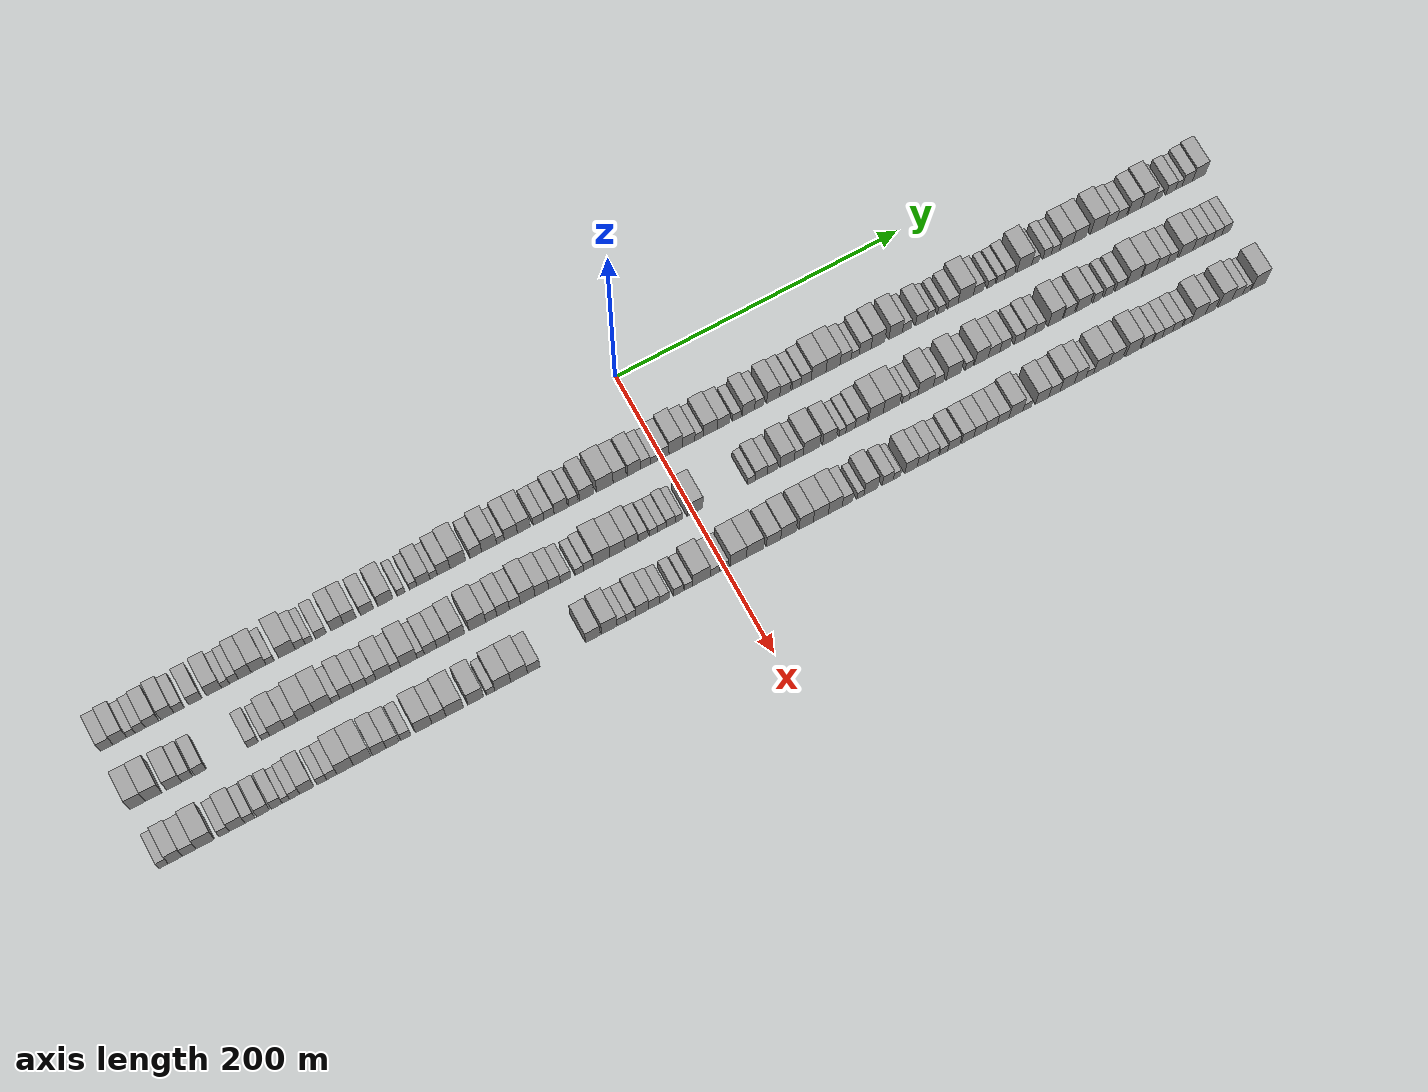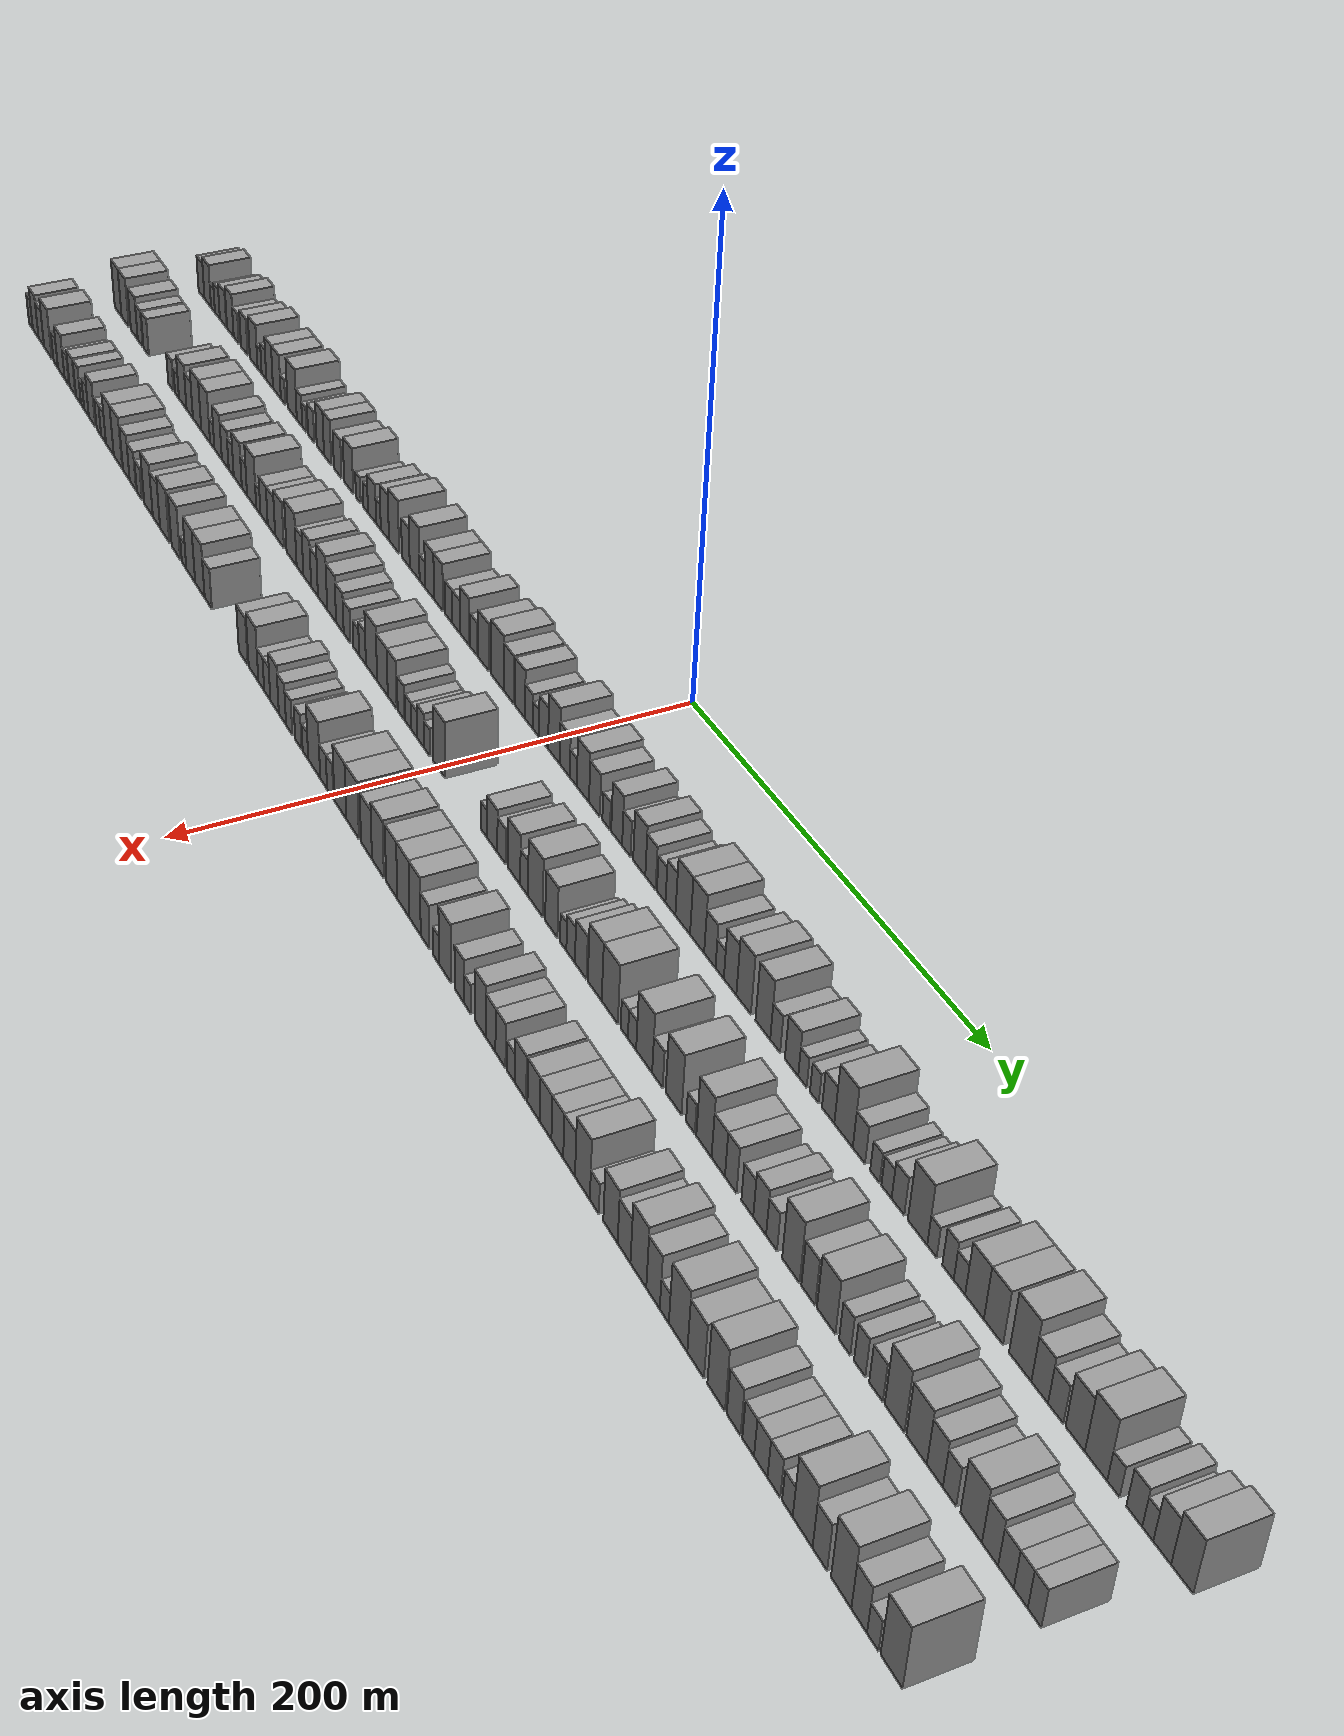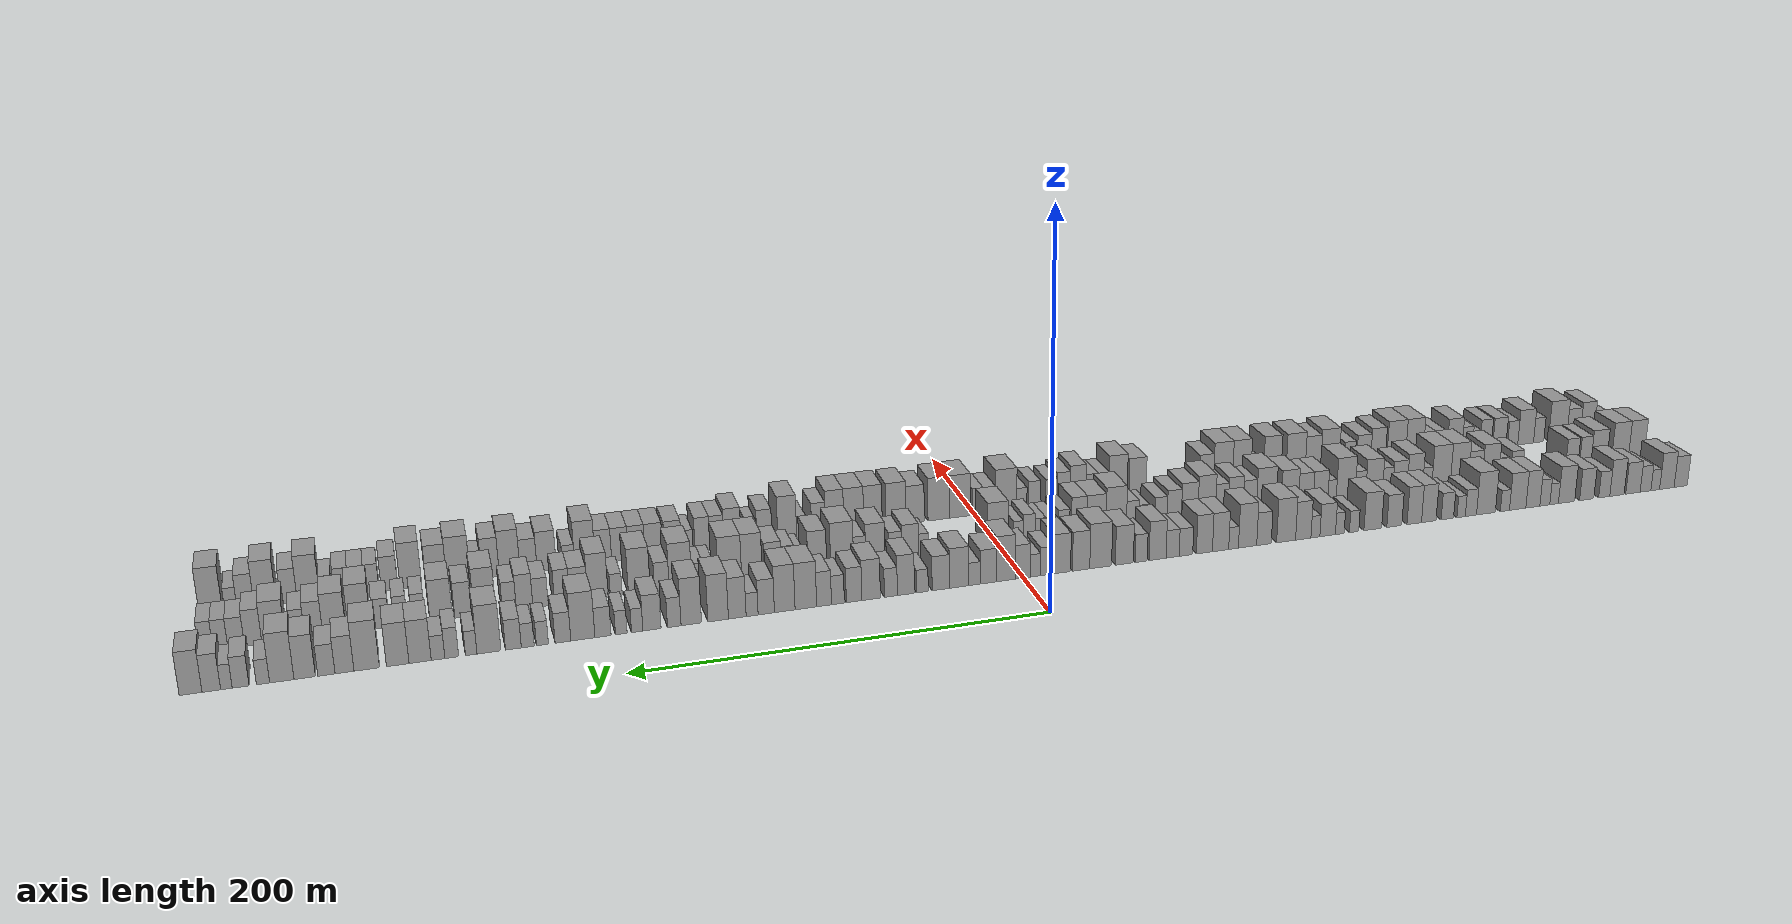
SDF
<sdf version="1.6">
 <world name="default">
  <scene>
   <sky><clouds><speed>12</speed></clouds></sky>
   <ambient>0.4 0.4 0.4 1</ambient>
   <background>0.7 0.7 0.7 1</background>
   <shadows>1</shadows>
  </scene>
  <gravity>0 0 -9.8066</gravity>
  <magnetic_field>6e-06 2.3e-05 -4.2e-05</magnetic_field>
  <physics default="0" name="default_physics" type="ode">
   <ode>
    <solver>
     <type>quick</type>
     <iters>10</iters>
     <sor>1.0</sor>
     <use_dynamic_moi_rescaling>0</use_dynamic_moi_rescaling>
    </solver>
    <constraints>
     <cfm>0</cfm>
     <erp>0.2</erp>
     <contact_max_correcting_vel>100</contact_max_correcting_vel>
     <contact_surface_layer>0.001</contact_surface_layer>
    </constraints>
   </ode>
   <max_step_size>0.004</max_step_size>
   <real_time_factor>1</real_time_factor>
   <real_time_update_rate>250</real_time_update_rate>
  </physics>
  <light name="sun" type="directional">
   <pose>0 0 10 0 0 0</pose>
   <diffuse>0.8 0.8 0.8 1</diffuse>
   <specular>0.2 0.2 0.2 1</specular>
   <attenuation>
    <range>1000</range>
    <constant>0.9</constant>
    <linear>0.01</linear>
    <quadratic>0.001</quadratic>
   </attenuation>
   <direction>-0.5 0.1 -0.9</direction>
  </light>
  <model name="building_1">
   <static>1</static>
   <pose>50.0000 -375.8266 0 0.000000 0.000000 0.000000</pose>
   <link name="link">
    <pose>0 0 9.00 0 0 0</pose>
    <collision name="collision"><geometry><box><size>20.0000 8.3468 18.0000</size></box></geometry></collision>
    <visual name="visual">
     <cast_shadows>0</cast_shadows>
     <geometry><box><size>20.0000 8.3468 18.0000</size></box></geometry>
     <material>
      <script>
       <uri>model://grey_wall/materials/scripts</uri>
       <uri>model://grey_wall/materials/textures</uri>
       <name>vrc/grey_wall</name>
      </script>
     </material>
    </visual>
   </link>
  </model>
  <model name="building_2">
   <static>1</static>
   <pose>50.0000 -367.0918 0 0.000000 0.000000 0.000000</pose>
   <link name="link">
    <pose>0 0 10.50 0 0 0</pose>
    <collision name="collision"><geometry><box><size>20.0000 9.1228 21.0000</size></box></geometry></collision>
    <visual name="visual">
     <cast_shadows>0</cast_shadows>
     <geometry><box><size>20.0000 9.1228 21.0000</size></box></geometry>
     <material>
      <script>
       <uri>model://grey_wall/materials/scripts</uri>
       <uri>model://grey_wall/materials/textures</uri>
       <name>vrc/grey_wall</name>
      </script>
     </material>
    </visual>
   </link>
  </model>
  <model name="building_3">
   <static>1</static>
   <pose>50.0000 -359.8040 0 0.000000 0.000000 0.000000</pose>
   <link name="link">
    <pose>0 0 6.00 0 0 0</pose>
    <collision name="collision"><geometry><box><size>20.0000 5.4529 12.0000</size></box></geometry></collision>
    <visual name="visual">
     <cast_shadows>0</cast_shadows>
     <geometry><box><size>20.0000 5.4529 12.0000</size></box></geometry>
     <material>
      <script>
       <uri>model://grey_wall/materials/scripts</uri>
       <uri>model://grey_wall/materials/textures</uri>
       <name>vrc/grey_wall</name>
      </script>
     </material>
    </visual>
   </link>
  </model>
  <model name="building_4">
   <static>1</static>
   <pose>50.0000 -353.6769 0 0.000000 0.000000 0.000000</pose>
   <link name="link">
    <pose>0 0 7.50 0 0 0</pose>
    <collision name="collision"><geometry><box><size>20.0000 6.8014 15.0000</size></box></geometry></collision>
    <visual name="visual">
     <cast_shadows>0</cast_shadows>
     <geometry><box><size>20.0000 6.8014 15.0000</size></box></geometry>
     <material>
      <script>
       <uri>model://grey_wall/materials/scripts</uri>
       <uri>model://grey_wall/materials/textures</uri>
       <name>vrc/grey_wall</name>
      </script>
     </material>
    </visual>
   </link>
  </model>
  <model name="building_5">
   <static>1</static>
   <pose>50.0000 -345.8114 0 0.000000 0.000000 0.000000</pose>
   <link name="link">
    <pose>0 0 9.00 0 0 0</pose>
    <collision name="collision"><geometry><box><size>20.0000 8.9297 18.0000</size></box></geometry></collision>
    <visual name="visual">
     <cast_shadows>0</cast_shadows>
     <geometry><box><size>20.0000 8.9297 18.0000</size></box></geometry>
     <material>
      <script>
       <uri>model://grey_wall/materials/scripts</uri>
       <uri>model://grey_wall/materials/textures</uri>
       <name>vrc/grey_wall</name>
      </script>
     </material>
    </visual>
   </link>
  </model>
  <model name="building_6">
   <static>1</static>
   <pose>50.0000 -335.8831 0 0.000000 0.000000 0.000000</pose>
   <link name="link">
    <pose>0 0 10.50 0 0 0</pose>
    <collision name="collision"><geometry><box><size>20.0000 8.9269 21.0000</size></box></geometry></collision>
    <visual name="visual">
     <cast_shadows>0</cast_shadows>
     <geometry><box><size>20.0000 8.9269 21.0000</size></box></geometry>
     <material>
      <script>
       <uri>model://grey_wall/materials/scripts</uri>
       <uri>model://grey_wall/materials/textures</uri>
       <name>vrc/grey_wall</name>
      </script>
     </material>
    </visual>
   </link>
  </model>
  <model name="building_7">
   <static>1</static>
   <pose>50.0000 -327.9880 0 0.000000 0.000000 0.000000</pose>
   <link name="link">
    <pose>0 0 7.50 0 0 0</pose>
    <collision name="collision"><geometry><box><size>20.0000 6.8631 15.0000</size></box></geometry></collision>
    <visual name="visual">
     <cast_shadows>0</cast_shadows>
     <geometry><box><size>20.0000 6.8631 15.0000</size></box></geometry>
     <material>
      <script>
       <uri>model://grey_wall/materials/scripts</uri>
       <uri>model://grey_wall/materials/textures</uri>
       <name>vrc/grey_wall</name>
      </script>
     </material>
    </visual>
   </link>
  </model>
  <model name="building_8">
   <static>1</static>
   <pose>50.0000 -317.1710 0 0.000000 0.000000 0.000000</pose>
   <link name="link">
    <pose>0 0 9.00 0 0 0</pose>
    <collision name="collision"><geometry><box><size>20.0000 8.7710 18.0000</size></box></geometry></collision>
    <visual name="visual">
     <cast_shadows>0</cast_shadows>
     <geometry><box><size>20.0000 8.7710 18.0000</size></box></geometry>
     <material>
      <script>
       <uri>model://grey_wall/materials/scripts</uri>
       <uri>model://grey_wall/materials/textures</uri>
       <name>vrc/grey_wall</name>
      </script>
     </material>
    </visual>
   </link>
  </model>
  <model name="building_9">
   <static>1</static>
   <pose>50.0000 -304.8281 0 0.000000 0.000000 0.000000</pose>
   <link name="link">
    <pose>0 0 10.50 0 0 0</pose>
    <collision name="collision"><geometry><box><size>20.0000 9.9147 21.0000</size></box></geometry></collision>
    <visual name="visual">
     <cast_shadows>0</cast_shadows>
     <geometry><box><size>20.0000 9.9147 21.0000</size></box></geometry>
     <material>
      <script>
       <uri>model://grey_wall/materials/scripts</uri>
       <uri>model://grey_wall/materials/textures</uri>
       <name>vrc/grey_wall</name>
      </script>
     </material>
    </visual>
   </link>
  </model>
  <model name="building_10">
   <static>1</static>
   <pose>50.0000 -297.2527 0 0.000000 0.000000 0.000000</pose>
   <link name="link">
    <pose>0 0 6.00 0 0 0</pose>
    <collision name="collision"><geometry><box><size>20.0000 5.2360 12.0000</size></box></geometry></collision>
    <visual name="visual">
     <cast_shadows>0</cast_shadows>
     <geometry><box><size>20.0000 5.2360 12.0000</size></box></geometry>
     <material>
      <script>
       <uri>model://grey_wall/materials/scripts</uri>
       <uri>model://grey_wall/materials/textures</uri>
       <name>vrc/grey_wall</name>
      </script>
     </material>
    </visual>
   </link>
  </model>
  <model name="building_11">
   <static>1</static>
   <pose>50.0000 -291.6268 0 0.000000 0.000000 0.000000</pose>
   <link name="link">
    <pose>0 0 7.50 0 0 0</pose>
    <collision name="collision"><geometry><box><size>20.0000 6.0158 15.0000</size></box></geometry></collision>
    <visual name="visual">
     <cast_shadows>0</cast_shadows>
     <geometry><box><size>20.0000 6.0158 15.0000</size></box></geometry>
     <material>
      <script>
       <uri>model://grey_wall/materials/scripts</uri>
       <uri>model://grey_wall/materials/textures</uri>
       <name>vrc/grey_wall</name>
      </script>
     </material>
    </visual>
   </link>
  </model>
  <model name="building_12">
   <static>1</static>
   <pose>50.0000 -284.3805 0 0.000000 0.000000 0.000000</pose>
   <link name="link">
    <pose>0 0 10.50 0 0 0</pose>
    <collision name="collision"><geometry><box><size>20.0000 8.4769 21.0000</size></box></geometry></collision>
    <visual name="visual">
     <cast_shadows>0</cast_shadows>
     <geometry><box><size>20.0000 8.4769 21.0000</size></box></geometry>
     <material>
      <script>
       <uri>model://grey_wall/materials/scripts</uri>
       <uri>model://grey_wall/materials/textures</uri>
       <name>vrc/grey_wall</name>
      </script>
     </material>
    </visual>
   </link>
  </model>
  <model name="building_13">
   <static>1</static>
   <pose>50.0000 -275.2082 0 0.000000 0.000000 0.000000</pose>
   <link name="link">
    <pose>0 0 10.50 0 0 0</pose>
    <collision name="collision"><geometry><box><size>20.0000 9.8677 21.0000</size></box></geometry></collision>
    <visual name="visual">
     <cast_shadows>0</cast_shadows>
     <geometry><box><size>20.0000 9.8677 21.0000</size></box></geometry>
     <material>
      <script>
       <uri>model://grey_wall/materials/scripts</uri>
       <uri>model://grey_wall/materials/textures</uri>
       <name>vrc/grey_wall</name>
      </script>
     </material>
    </visual>
   </link>
  </model>
  <model name="building_14">
   <static>1</static>
   <pose>50.0000 -267.5446 0 0.000000 0.000000 0.000000</pose>
   <link name="link">
    <pose>0 0 6.00 0 0 0</pose>
    <collision name="collision"><geometry><box><size>20.0000 5.4594 12.0000</size></box></geometry></collision>
    <visual name="visual">
     <cast_shadows>0</cast_shadows>
     <geometry><box><size>20.0000 5.4594 12.0000</size></box></geometry>
     <material>
      <script>
       <uri>model://grey_wall/materials/scripts</uri>
       <uri>model://grey_wall/materials/textures</uri>
       <name>vrc/grey_wall</name>
      </script>
     </material>
    </visual>
   </link>
  </model>
  <model name="building_15">
   <static>1</static>
   <pose>50.0000 -256.2047 0 0.000000 0.000000 0.000000</pose>
   <link name="link">
    <pose>0 0 12.00 0 0 0</pose>
    <collision name="collision"><geometry><box><size>20.0000 11.2203 24.0000</size></box></geometry></collision>
    <visual name="visual">
     <cast_shadows>0</cast_shadows>
     <geometry><box><size>20.0000 11.2203 24.0000</size></box></geometry>
     <material>
      <script>
       <uri>model://grey_wall/materials/scripts</uri>
       <uri>model://grey_wall/materials/textures</uri>
       <name>vrc/grey_wall</name>
      </script>
     </material>
    </visual>
   </link>
  </model>
  <model name="building_16">
   <static>1</static>
   <pose>50.0000 -247.2820 0 0.000000 0.000000 0.000000</pose>
   <link name="link">
    <pose>0 0 7.50 0 0 0</pose>
    <collision name="collision"><geometry><box><size>20.0000 6.6251 15.0000</size></box></geometry></collision>
    <visual name="visual">
     <cast_shadows>0</cast_shadows>
     <geometry><box><size>20.0000 6.6251 15.0000</size></box></geometry>
     <material>
      <script>
       <uri>model://grey_wall/materials/scripts</uri>
       <uri>model://grey_wall/materials/textures</uri>
       <name>vrc/grey_wall</name>
      </script>
     </material>
    </visual>
   </link>
  </model>
  <model name="building_17">
   <static>1</static>
   <pose>50.0000 -241.4940 0 0.000000 0.000000 0.000000</pose>
   <link name="link">
    <pose>0 0 6.00 0 0 0</pose>
    <collision name="collision"><geometry><box><size>20.0000 4.9509 12.0000</size></box></geometry></collision>
    <visual name="visual">
     <cast_shadows>0</cast_shadows>
     <geometry><box><size>20.0000 4.9509 12.0000</size></box></geometry>
     <material>
      <script>
       <uri>model://grey_wall/materials/scripts</uri>
       <uri>model://grey_wall/materials/textures</uri>
       <name>vrc/grey_wall</name>
      </script>
     </material>
    </visual>
   </link>
  </model>
  <model name="building_18">
   <static>1</static>
   <pose>50.0000 -233.3700 0 0.000000 0.000000 0.000000</pose>
   <link name="link">
    <pose>0 0 7.50 0 0 0</pose>
    <collision name="collision"><geometry><box><size>20.0000 7.2971 15.0000</size></box></geometry></collision>
    <visual name="visual">
     <cast_shadows>0</cast_shadows>
     <geometry><box><size>20.0000 7.2971 15.0000</size></box></geometry>
     <material>
      <script>
       <uri>model://grey_wall/materials/scripts</uri>
       <uri>model://grey_wall/materials/textures</uri>
       <name>vrc/grey_wall</name>
      </script>
     </material>
    </visual>
   </link>
  </model>
  <model name="building_19">
   <static>1</static>
   <pose>50.0000 -222.4704 0 0.000000 0.000000 0.000000</pose>
   <link name="link">
    <pose>0 0 10.50 0 0 0</pose>
    <collision name="collision"><geometry><box><size>20.0000 8.5022 21.0000</size></box></geometry></collision>
    <visual name="visual">
     <cast_shadows>0</cast_shadows>
     <geometry><box><size>20.0000 8.5022 21.0000</size></box></geometry>
     <material>
      <script>
       <uri>model://grey_wall/materials/scripts</uri>
       <uri>model://grey_wall/materials/textures</uri>
       <name>vrc/grey_wall</name>
      </script>
     </material>
    </visual>
   </link>
  </model>
  <model name="building_20">
   <static>1</static>
   <pose>50.0000 -213.9884 0 0.000000 0.000000 0.000000</pose>
   <link name="link">
    <pose>0 0 10.50 0 0 0</pose>
    <collision name="collision"><geometry><box><size>20.0000 8.4618 21.0000</size></box></geometry></collision>
    <visual name="visual">
     <cast_shadows>0</cast_shadows>
     <geometry><box><size>20.0000 8.4618 21.0000</size></box></geometry>
     <material>
      <script>
       <uri>model://grey_wall/materials/scripts</uri>
       <uri>model://grey_wall/materials/textures</uri>
       <name>vrc/grey_wall</name>
      </script>
     </material>
    </visual>
   </link>
  </model>
  <model name="building_21">
   <static>1</static>
   <pose>50.0000 -202.4168 0 0.000000 0.000000 0.000000</pose>
   <link name="link">
    <pose>0 0 9.00 0 0 0</pose>
    <collision name="collision"><geometry><box><size>20.0000 8.6815 18.0000</size></box></geometry></collision>
    <visual name="visual">
     <cast_shadows>0</cast_shadows>
     <geometry><box><size>20.0000 8.6815 18.0000</size></box></geometry>
     <material>
      <script>
       <uri>model://grey_wall/materials/scripts</uri>
       <uri>model://grey_wall/materials/textures</uri>
       <name>vrc/grey_wall</name>
      </script>
     </material>
    </visual>
   </link>
  </model>
  <model name="building_22">
   <static>1</static>
   <pose>50.0000 -189.9967 0 0.000000 0.000000 0.000000</pose>
   <link name="link">
    <pose>0 0 10.50 0 0 0</pose>
    <collision name="collision"><geometry><box><size>20.0000 10.1585 21.0000</size></box></geometry></collision>
    <visual name="visual">
     <cast_shadows>0</cast_shadows>
     <geometry><box><size>20.0000 10.1585 21.0000</size></box></geometry>
     <material>
      <script>
       <uri>model://grey_wall/materials/scripts</uri>
       <uri>model://grey_wall/materials/textures</uri>
       <name>vrc/grey_wall</name>
      </script>
     </material>
    </visual>
   </link>
  </model>
  <model name="building_23">
   <static>1</static>
   <pose>50.0000 -179.2774 0 0.000000 0.000000 0.000000</pose>
   <link name="link">
    <pose>0 0 6.00 0 0 0</pose>
    <collision name="collision"><geometry><box><size>20.0000 5.2801 12.0000</size></box></geometry></collision>
    <visual name="visual">
     <cast_shadows>0</cast_shadows>
     <geometry><box><size>20.0000 5.2801 12.0000</size></box></geometry>
     <material>
      <script>
       <uri>model://grey_wall/materials/scripts</uri>
       <uri>model://grey_wall/materials/textures</uri>
       <name>vrc/grey_wall</name>
      </script>
     </material>
    </visual>
   </link>
  </model>
  <model name="building_24">
   <static>1</static>
   <pose>50.0000 -171.1442 0 0.000000 0.000000 0.000000</pose>
   <link name="link">
    <pose>0 0 6.00 0 0 0</pose>
    <collision name="collision"><geometry><box><size>20.0000 4.9862 12.0000</size></box></geometry></collision>
    <visual name="visual">
     <cast_shadows>0</cast_shadows>
     <geometry><box><size>20.0000 4.9862 12.0000</size></box></geometry>
     <material>
      <script>
       <uri>model://grey_wall/materials/scripts</uri>
       <uri>model://grey_wall/materials/textures</uri>
       <name>vrc/grey_wall</name>
      </script>
     </material>
    </visual>
   </link>
  </model>
  <model name="building_25">
   <static>1</static>
   <pose>50.0000 -164.2541 0 0.000000 0.000000 0.000000</pose>
   <link name="link">
    <pose>0 0 9.00 0 0 0</pose>
    <collision name="collision"><geometry><box><size>20.0000 8.7940 18.0000</size></box></geometry></collision>
    <visual name="visual">
     <cast_shadows>0</cast_shadows>
     <geometry><box><size>20.0000 8.7940 18.0000</size></box></geometry>
     <material>
      <script>
       <uri>model://grey_wall/materials/scripts</uri>
       <uri>model://grey_wall/materials/textures</uri>
       <name>vrc/grey_wall</name>
      </script>
     </material>
    </visual>
   </link>
  </model>
  <model name="building_26">
   <static>1</static>
   <pose>50.0000 -157.3276 0 0.000000 0.000000 0.000000</pose>
   <link name="link">
    <pose>0 0 6.00 0 0 0</pose>
    <collision name="collision"><geometry><box><size>20.0000 5.0589 12.0000</size></box></geometry></collision>
    <visual name="visual">
     <cast_shadows>0</cast_shadows>
     <geometry><box><size>20.0000 5.0589 12.0000</size></box></geometry>
     <material>
      <script>
       <uri>model://grey_wall/materials/scripts</uri>
       <uri>model://grey_wall/materials/textures</uri>
       <name>vrc/grey_wall</name>
      </script>
     </material>
    </visual>
   </link>
  </model>
  <model name="building_27">
   <static>1</static>
   <pose>50.0000 -150.4753 0 0.000000 0.000000 0.000000</pose>
   <link name="link">
    <pose>0 0 10.50 0 0 0</pose>
    <collision name="collision"><geometry><box><size>20.0000 8.6458 21.0000</size></box></geometry></collision>
    <visual name="visual">
     <cast_shadows>0</cast_shadows>
     <geometry><box><size>20.0000 8.6458 21.0000</size></box></geometry>
     <material>
      <script>
       <uri>model://grey_wall/materials/scripts</uri>
       <uri>model://grey_wall/materials/textures</uri>
       <name>vrc/grey_wall</name>
      </script>
     </material>
    </visual>
   </link>
  </model>
  <model name="building_28">
   <static>1</static>
   <pose>50.0000 -140.8571 0 0.000000 0.000000 0.000000</pose>
   <link name="link">
    <pose>0 0 12.00 0 0 0</pose>
    <collision name="collision"><geometry><box><size>20.0000 10.5905 24.0000</size></box></geometry></collision>
    <visual name="visual">
     <cast_shadows>0</cast_shadows>
     <geometry><box><size>20.0000 10.5905 24.0000</size></box></geometry>
     <material>
      <script>
       <uri>model://grey_wall/materials/scripts</uri>
       <uri>model://grey_wall/materials/textures</uri>
       <name>vrc/grey_wall</name>
      </script>
     </material>
    </visual>
   </link>
  </model>
  <model name="building_29">
   <static>1</static>
   <pose>50.0000 -128.5230 0 0.000000 0.000000 0.000000</pose>
   <link name="link">
    <pose>0 0 9.00 0 0 0</pose>
    <collision name="collision"><geometry><box><size>20.0000 8.0777 18.0000</size></box></geometry></collision>
    <visual name="visual">
     <cast_shadows>0</cast_shadows>
     <geometry><box><size>20.0000 8.0777 18.0000</size></box></geometry>
     <material>
      <script>
       <uri>model://grey_wall/materials/scripts</uri>
       <uri>model://grey_wall/materials/textures</uri>
       <name>vrc/grey_wall</name>
      </script>
     </material>
    </visual>
   </link>
  </model>
  <model name="building_30">
   <static>1</static>
   <pose>50.0000 -119.4257 0 0.000000 0.000000 0.000000</pose>
   <link name="link">
    <pose>0 0 12.00 0 0 0</pose>
    <collision name="collision"><geometry><box><size>20.0000 10.1169 24.0000</size></box></geometry></collision>
    <visual name="visual">
     <cast_shadows>0</cast_shadows>
     <geometry><box><size>20.0000 10.1169 24.0000</size></box></geometry>
     <material>
      <script>
       <uri>model://grey_wall/materials/scripts</uri>
       <uri>model://grey_wall/materials/textures</uri>
       <name>vrc/grey_wall</name>
      </script>
     </material>
    </visual>
   </link>
  </model>
  <model name="building_31">
   <static>1</static>
   <pose>50.0000 -111.6893 0 0.000000 0.000000 0.000000</pose>
   <link name="link">
    <pose>0 0 6.00 0 0 0</pose>
    <collision name="collision"><geometry><box><size>20.0000 5.3561 12.0000</size></box></geometry></collision>
    <visual name="visual">
     <cast_shadows>0</cast_shadows>
     <geometry><box><size>20.0000 5.3561 12.0000</size></box></geometry>
     <material>
      <script>
       <uri>model://grey_wall/materials/scripts</uri>
       <uri>model://grey_wall/materials/textures</uri>
       <name>vrc/grey_wall</name>
      </script>
     </material>
    </visual>
   </link>
  </model>
  <model name="building_32">
   <static>1</static>
   <pose>50.0000 -104.5540 0 0.000000 0.000000 0.000000</pose>
   <link name="link">
    <pose>0 0 10.50 0 0 0</pose>
    <collision name="collision"><geometry><box><size>20.0000 8.9144 21.0000</size></box></geometry></collision>
    <visual name="visual">
     <cast_shadows>0</cast_shadows>
     <geometry><box><size>20.0000 8.9144 21.0000</size></box></geometry>
     <material>
      <script>
       <uri>model://grey_wall/materials/scripts</uri>
       <uri>model://grey_wall/materials/textures</uri>
       <name>vrc/grey_wall</name>
      </script>
     </material>
    </visual>
   </link>
  </model>
  <model name="building_33">
   <static>1</static>
   <pose>50.0000 -95.7066 0 0.000000 0.000000 0.000000</pose>
   <link name="link">
    <pose>0 0 10.50 0 0 0</pose>
    <collision name="collision"><geometry><box><size>20.0000 8.7805 21.0000</size></box></geometry></collision>
    <visual name="visual">
     <cast_shadows>0</cast_shadows>
     <geometry><box><size>20.0000 8.7805 21.0000</size></box></geometry>
     <material>
      <script>
       <uri>model://grey_wall/materials/scripts</uri>
       <uri>model://grey_wall/materials/textures</uri>
       <name>vrc/grey_wall</name>
      </script>
     </material>
    </visual>
   </link>
  </model>
  <model name="building_34">
   <static>1</static>
   <pose>50.0000 -85.6473 0 0.000000 0.000000 0.000000</pose>
   <link name="link">
    <pose>0 0 7.50 0 0 0</pose>
    <collision name="collision"><geometry><box><size>20.0000 7.3380 15.0000</size></box></geometry></collision>
    <visual name="visual">
     <cast_shadows>0</cast_shadows>
     <geometry><box><size>20.0000 7.3380 15.0000</size></box></geometry>
     <material>
      <script>
       <uri>model://grey_wall/materials/scripts</uri>
       <uri>model://grey_wall/materials/textures</uri>
       <name>vrc/grey_wall</name>
      </script>
     </material>
    </visual>
   </link>
  </model>
  <model name="building_35">
   <static>1</static>
   <pose>50.0000 -78.4366 0 0.000000 0.000000 0.000000</pose>
   <link name="link">
    <pose>0 0 7.50 0 0 0</pose>
    <collision name="collision"><geometry><box><size>20.0000 7.0835 15.0000</size></box></geometry></collision>
    <visual name="visual">
     <cast_shadows>0</cast_shadows>
     <geometry><box><size>20.0000 7.0835 15.0000</size></box></geometry>
     <material>
      <script>
       <uri>model://grey_wall/materials/scripts</uri>
       <uri>model://grey_wall/materials/textures</uri>
       <name>vrc/grey_wall</name>
      </script>
     </material>
    </visual>
   </link>
  </model>
  <model name="building_36">
   <static>1</static>
   <pose>50.0000 -70.3378 0 0.000000 0.000000 0.000000</pose>
   <link name="link">
    <pose>0 0 10.50 0 0 0</pose>
    <collision name="collision"><geometry><box><size>20.0000 9.1141 21.0000</size></box></geometry></collision>
    <visual name="visual">
     <cast_shadows>0</cast_shadows>
     <geometry><box><size>20.0000 9.1141 21.0000</size></box></geometry>
     <material>
      <script>
       <uri>model://grey_wall/materials/scripts</uri>
       <uri>model://grey_wall/materials/textures</uri>
       <name>vrc/grey_wall</name>
      </script>
     </material>
    </visual>
   </link>
  </model>
  <model name="building_37">
   <static>1</static>
   <pose>50.0000 -61.5664 0 0.000000 0.000000 0.000000</pose>
   <link name="link">
    <pose>0 0 7.50 0 0 0</pose>
    <collision name="collision"><geometry><box><size>20.0000 6.4287 15.0000</size></box></geometry></collision>
    <visual name="visual">
     <cast_shadows>0</cast_shadows>
     <geometry><box><size>20.0000 6.4287 15.0000</size></box></geometry>
     <material>
      <script>
       <uri>model://grey_wall/materials/scripts</uri>
       <uri>model://grey_wall/materials/textures</uri>
       <name>vrc/grey_wall</name>
      </script>
     </material>
    </visual>
   </link>
  </model>
  <model name="building_38">
   <static>1</static>
   <pose>50.0000 -52.5485 0 0.000000 0.000000 0.000000</pose>
   <link name="link">
    <pose>0 0 10.50 0 0 0</pose>
    <collision name="collision"><geometry><box><size>20.0000 9.6071 21.0000</size></box></geometry></collision>
    <visual name="visual">
     <cast_shadows>0</cast_shadows>
     <geometry><box><size>20.0000 9.6071 21.0000</size></box></geometry>
     <material>
      <script>
       <uri>model://grey_wall/materials/scripts</uri>
       <uri>model://grey_wall/materials/textures</uri>
       <name>vrc/grey_wall</name>
      </script>
     </material>
    </visual>
   </link>
  </model>
  <model name="building_39">
   <static>1</static>
   <pose>50.0000 -39.9715 0 0.000000 0.000000 0.000000</pose>
   <link name="link">
    <pose>0 0 12.00 0 0 0</pose>
    <collision name="collision"><geometry><box><size>20.0000 11.5470 24.0000</size></box></geometry></collision>
    <visual name="visual">
     <cast_shadows>0</cast_shadows>
     <geometry><box><size>20.0000 11.5470 24.0000</size></box></geometry>
     <material>
      <script>
       <uri>model://grey_wall/materials/scripts</uri>
       <uri>model://grey_wall/materials/textures</uri>
       <name>vrc/grey_wall</name>
      </script>
     </material>
    </visual>
   </link>
  </model>
  <model name="building_40">
   <static>1</static>
   <pose>50.0000 -29.6646 0 0.000000 0.000000 0.000000</pose>
   <link name="link">
    <pose>0 0 10.50 0 0 0</pose>
    <collision name="collision"><geometry><box><size>20.0000 9.0667 21.0000</size></box></geometry></collision>
    <visual name="visual">
     <cast_shadows>0</cast_shadows>
     <geometry><box><size>20.0000 9.0667 21.0000</size></box></geometry>
     <material>
      <script>
       <uri>model://grey_wall/materials/scripts</uri>
       <uri>model://grey_wall/materials/textures</uri>
       <name>vrc/grey_wall</name>
      </script>
     </material>
    </visual>
   </link>
  </model>
  <model name="building_41">
   <static>1</static>
   <pose>50.0000 -19.7086 0 0.000000 0.000000 0.000000</pose>
   <link name="link">
    <pose>0 0 10.50 0 0 0</pose>
    <collision name="collision"><geometry><box><size>20.0000 8.8454 21.0000</size></box></geometry></collision>
    <visual name="visual">
     <cast_shadows>0</cast_shadows>
     <geometry><box><size>20.0000 8.8454 21.0000</size></box></geometry>
     <material>
      <script>
       <uri>model://grey_wall/materials/scripts</uri>
       <uri>model://grey_wall/materials/textures</uri>
       <name>vrc/grey_wall</name>
      </script>
     </material>
    </visual>
   </link>
  </model>
  <model name="building_42">
   <static>1</static>
   <pose>50.0000 -11.8778 0 0.000000 0.000000 0.000000</pose>
   <link name="link">
    <pose>0 0 7.50 0 0 0</pose>
    <collision name="collision"><geometry><box><size>20.0000 6.8161 15.0000</size></box></geometry></collision>
    <visual name="visual">
     <cast_shadows>0</cast_shadows>
     <geometry><box><size>20.0000 6.8161 15.0000</size></box></geometry>
     <material>
      <script>
       <uri>model://grey_wall/materials/scripts</uri>
       <uri>model://grey_wall/materials/textures</uri>
       <name>vrc/grey_wall</name>
      </script>
     </material>
    </visual>
   </link>
  </model>
  <model name="building_43">
   <static>1</static>
   <pose>50.0000 -5.8425 0 0.000000 0.000000 0.000000</pose>
   <link name="link">
    <pose>0 0 6.00 0 0 0</pose>
    <collision name="collision"><geometry><box><size>20.0000 5.2546 12.0000</size></box></geometry></collision>
    <visual name="visual">
     <cast_shadows>0</cast_shadows>
     <geometry><box><size>20.0000 5.2546 12.0000</size></box></geometry>
     <material>
      <script>
       <uri>model://grey_wall/materials/scripts</uri>
       <uri>model://grey_wall/materials/textures</uri>
       <name>vrc/grey_wall</name>
      </script>
     </material>
    </visual>
   </link>
  </model>
  <model name="building_44">
   <static>1</static>
   <pose>50.0000 0.6852 0 0.000000 0.000000 0.000000</pose>
   <link name="link">
    <pose>0 0 9.00 0 0 0</pose>
    <collision name="collision"><geometry><box><size>20.0000 7.8006 18.0000</size></box></geometry></collision>
    <visual name="visual">
     <cast_shadows>0</cast_shadows>
     <geometry><box><size>20.0000 7.8006 18.0000</size></box></geometry>
     <material>
      <script>
       <uri>model://grey_wall/materials/scripts</uri>
       <uri>model://grey_wall/materials/textures</uri>
       <name>vrc/grey_wall</name>
      </script>
     </material>
    </visual>
   </link>
  </model>
  <model name="building_45">
   <static>1</static>
   <pose>50.0000 9.4285 0 0.000000 0.000000 0.000000</pose>
   <link name="link">
    <pose>0 0 12.00 0 0 0</pose>
    <collision name="collision"><geometry><box><size>20.0000 9.6860 24.0000</size></box></geometry></collision>
    <visual name="visual">
     <cast_shadows>0</cast_shadows>
     <geometry><box><size>20.0000 9.6860 24.0000</size></box></geometry>
     <material>
      <script>
       <uri>model://grey_wall/materials/scripts</uri>
       <uri>model://grey_wall/materials/textures</uri>
       <name>vrc/grey_wall</name>
      </script>
     </material>
    </visual>
   </link>
  </model>
  <model name="building_46">
   <static>1</static>
   <pose>50.0000 18.4736 0 0.000000 0.000000 0.000000</pose>
   <link name="link">
    <pose>0 0 9.00 0 0 0</pose>
    <collision name="collision"><geometry><box><size>20.0000 8.4042 18.0000</size></box></geometry></collision>
    <visual name="visual">
     <cast_shadows>0</cast_shadows>
     <geometry><box><size>20.0000 8.4042 18.0000</size></box></geometry>
     <material>
      <script>
       <uri>model://grey_wall/materials/scripts</uri>
       <uri>model://grey_wall/materials/textures</uri>
       <name>vrc/grey_wall</name>
      </script>
     </material>
    </visual>
   </link>
  </model>
  <model name="building_47">
   <static>1</static>
   <pose>50.0000 25.5495 0 0.000000 0.000000 0.000000</pose>
   <link name="link">
    <pose>0 0 6.00 0 0 0</pose>
    <collision name="collision"><geometry><box><size>20.0000 5.7476 12.0000</size></box></geometry></collision>
    <visual name="visual">
     <cast_shadows>0</cast_shadows>
     <geometry><box><size>20.0000 5.7476 12.0000</size></box></geometry>
     <material>
      <script>
       <uri>model://grey_wall/materials/scripts</uri>
       <uri>model://grey_wall/materials/textures</uri>
       <name>vrc/grey_wall</name>
      </script>
     </material>
    </visual>
   </link>
  </model>
  <model name="building_48">
   <static>1</static>
   <pose>50.0000 33.4192 0 0.000000 0.000000 0.000000</pose>
   <link name="link">
    <pose>0 0 10.50 0 0 0</pose>
    <collision name="collision"><geometry><box><size>20.0000 9.9916 21.0000</size></box></geometry></collision>
    <visual name="visual">
     <cast_shadows>0</cast_shadows>
     <geometry><box><size>20.0000 9.9916 21.0000</size></box></geometry>
     <material>
      <script>
       <uri>model://grey_wall/materials/scripts</uri>
       <uri>model://grey_wall/materials/textures</uri>
       <name>vrc/grey_wall</name>
      </script>
     </material>
    </visual>
   </link>
  </model>
  <model name="building_49">
   <static>1</static>
   <pose>50.0000 42.7429 0 0.000000 0.000000 0.000000</pose>
   <link name="link">
    <pose>0 0 9.00 0 0 0</pose>
    <collision name="collision"><geometry><box><size>20.0000 8.6559 18.0000</size></box></geometry></collision>
    <visual name="visual">
     <cast_shadows>0</cast_shadows>
     <geometry><box><size>20.0000 8.6559 18.0000</size></box></geometry>
     <material>
      <script>
       <uri>model://grey_wall/materials/scripts</uri>
       <uri>model://grey_wall/materials/textures</uri>
       <name>vrc/grey_wall</name>
      </script>
     </material>
    </visual>
   </link>
  </model>
  <model name="building_50">
   <static>1</static>
   <pose>50.0000 52.0302 0 0.000000 0.000000 0.000000</pose>
   <link name="link">
    <pose>0 0 6.00 0 0 0</pose>
    <collision name="collision"><geometry><box><size>20.0000 5.9188 12.0000</size></box></geometry></collision>
    <visual name="visual">
     <cast_shadows>0</cast_shadows>
     <geometry><box><size>20.0000 5.9188 12.0000</size></box></geometry>
     <material>
      <script>
       <uri>model://grey_wall/materials/scripts</uri>
       <uri>model://grey_wall/materials/textures</uri>
       <name>vrc/grey_wall</name>
      </script>
     </material>
    </visual>
   </link>
  </model>
  <model name="building_51">
   <static>1</static>
   <pose>50.0000 60.2455 0 0.000000 0.000000 0.000000</pose>
   <link name="link">
    <pose>0 0 10.50 0 0 0</pose>
    <collision name="collision"><geometry><box><size>20.0000 8.5118 21.0000</size></box></geometry></collision>
    <visual name="visual">
     <cast_shadows>0</cast_shadows>
     <geometry><box><size>20.0000 8.5118 21.0000</size></box></geometry>
     <material>
      <script>
       <uri>model://grey_wall/materials/scripts</uri>
       <uri>model://grey_wall/materials/textures</uri>
       <name>vrc/grey_wall</name>
      </script>
     </material>
    </visual>
   </link>
  </model>
  <model name="building_52">
   <static>1</static>
   <pose>50.0000 67.7341 0 0.000000 0.000000 0.000000</pose>
   <link name="link">
    <pose>0 0 7.50 0 0 0</pose>
    <collision name="collision"><geometry><box><size>20.0000 6.4653 15.0000</size></box></geometry></collision>
    <visual name="visual">
     <cast_shadows>0</cast_shadows>
     <geometry><box><size>20.0000 6.4653 15.0000</size></box></geometry>
     <material>
      <script>
       <uri>model://grey_wall/materials/scripts</uri>
       <uri>model://grey_wall/materials/textures</uri>
       <name>vrc/grey_wall</name>
      </script>
     </material>
    </visual>
   </link>
  </model>
  <model name="building_53">
   <static>1</static>
   <pose>50.0000 77.5523 0 0.000000 0.000000 0.000000</pose>
   <link name="link">
    <pose>0 0 10.50 0 0 0</pose>
    <collision name="collision"><geometry><box><size>20.0000 9.1711 21.0000</size></box></geometry></collision>
    <visual name="visual">
     <cast_shadows>0</cast_shadows>
     <geometry><box><size>20.0000 9.1711 21.0000</size></box></geometry>
     <material>
      <script>
       <uri>model://grey_wall/materials/scripts</uri>
       <uri>model://grey_wall/materials/textures</uri>
       <name>vrc/grey_wall</name>
      </script>
     </material>
    </visual>
   </link>
  </model>
  <model name="building_54">
   <static>1</static>
   <pose>50.0000 85.9416 0 0.000000 0.000000 0.000000</pose>
   <link name="link">
    <pose>0 0 9.00 0 0 0</pose>
    <collision name="collision"><geometry><box><size>20.0000 7.6076 18.0000</size></box></geometry></collision>
    <visual name="visual">
     <cast_shadows>0</cast_shadows>
     <geometry><box><size>20.0000 7.6076 18.0000</size></box></geometry>
     <material>
      <script>
       <uri>model://grey_wall/materials/scripts</uri>
       <uri>model://grey_wall/materials/textures</uri>
       <name>vrc/grey_wall</name>
      </script>
     </material>
    </visual>
   </link>
  </model>
  <model name="building_55">
   <static>1</static>
   <pose>50.0000 93.8959 0 0.000000 0.000000 0.000000</pose>
   <link name="link">
    <pose>0 0 7.50 0 0 0</pose>
    <collision name="collision"><geometry><box><size>20.0000 6.3009 15.0000</size></box></geometry></collision>
    <visual name="visual">
     <cast_shadows>0</cast_shadows>
     <geometry><box><size>20.0000 6.3009 15.0000</size></box></geometry>
     <material>
      <script>
       <uri>model://grey_wall/materials/scripts</uri>
       <uri>model://grey_wall/materials/textures</uri>
       <name>vrc/grey_wall</name>
      </script>
     </material>
    </visual>
   </link>
  </model>
  <model name="building_56">
   <static>1</static>
   <pose>50.0000 100.6572 0 0.000000 0.000000 0.000000</pose>
   <link name="link">
    <pose>0 0 9.00 0 0 0</pose>
    <collision name="collision"><geometry><box><size>20.0000 7.2218 18.0000</size></box></geometry></collision>
    <visual name="visual">
     <cast_shadows>0</cast_shadows>
     <geometry><box><size>20.0000 7.2218 18.0000</size></box></geometry>
     <material>
      <script>
       <uri>model://grey_wall/materials/scripts</uri>
       <uri>model://grey_wall/materials/textures</uri>
       <name>vrc/grey_wall</name>
      </script>
     </material>
    </visual>
   </link>
  </model>
  <model name="building_57">
   <static>1</static>
   <pose>50.0000 109.5075 0 0.000000 0.000000 0.000000</pose>
   <link name="link">
    <pose>0 0 12.00 0 0 0</pose>
    <collision name="collision"><geometry><box><size>20.0000 10.4787 24.0000</size></box></geometry></collision>
    <visual name="visual">
     <cast_shadows>0</cast_shadows>
     <geometry><box><size>20.0000 10.4787 24.0000</size></box></geometry>
     <material>
      <script>
       <uri>model://grey_wall/materials/scripts</uri>
       <uri>model://grey_wall/materials/textures</uri>
       <name>vrc/grey_wall</name>
      </script>
     </material>
    </visual>
   </link>
  </model>
  <model name="building_58">
   <static>1</static>
   <pose>50.0000 119.7320 0 0.000000 0.000000 0.000000</pose>
   <link name="link">
    <pose>0 0 12.00 0 0 0</pose>
    <collision name="collision"><geometry><box><size>20.0000 9.9702 24.0000</size></box></geometry></collision>
    <visual name="visual">
     <cast_shadows>0</cast_shadows>
     <geometry><box><size>20.0000 9.9702 24.0000</size></box></geometry>
     <material>
      <script>
       <uri>model://grey_wall/materials/scripts</uri>
       <uri>model://grey_wall/materials/textures</uri>
       <name>vrc/grey_wall</name>
      </script>
     </material>
    </visual>
   </link>
  </model>
  <model name="building_59">
   <static>1</static>
   <pose>50.0000 128.6351 0 0.000000 0.000000 0.000000</pose>
   <link name="link">
    <pose>0 0 9.00 0 0 0</pose>
    <collision name="collision"><geometry><box><size>20.0000 7.8361 18.0000</size></box></geometry></collision>
    <visual name="visual">
     <cast_shadows>0</cast_shadows>
     <geometry><box><size>20.0000 7.8361 18.0000</size></box></geometry>
     <material>
      <script>
       <uri>model://grey_wall/materials/scripts</uri>
       <uri>model://grey_wall/materials/textures</uri>
       <name>vrc/grey_wall</name>
      </script>
     </material>
    </visual>
   </link>
  </model>
  <model name="building_60">
   <static>1</static>
   <pose>50.0000 135.4179 0 0.000000 0.000000 0.000000</pose>
   <link name="link">
    <pose>0 0 6.00 0 0 0</pose>
    <collision name="collision"><geometry><box><size>20.0000 5.7295 12.0000</size></box></geometry></collision>
    <visual name="visual">
     <cast_shadows>0</cast_shadows>
     <geometry><box><size>20.0000 5.7295 12.0000</size></box></geometry>
     <material>
      <script>
       <uri>model://grey_wall/materials/scripts</uri>
       <uri>model://grey_wall/materials/textures</uri>
       <name>vrc/grey_wall</name>
      </script>
     </material>
    </visual>
   </link>
  </model>
  <model name="building_61">
   <static>1</static>
   <pose>50.0000 142.5011 0 0.000000 0.000000 0.000000</pose>
   <link name="link">
    <pose>0 0 10.50 0 0 0</pose>
    <collision name="collision"><geometry><box><size>20.0000 8.4368 21.0000</size></box></geometry></collision>
    <visual name="visual">
     <cast_shadows>0</cast_shadows>
     <geometry><box><size>20.0000 8.4368 21.0000</size></box></geometry>
     <material>
      <script>
       <uri>model://grey_wall/materials/scripts</uri>
       <uri>model://grey_wall/materials/textures</uri>
       <name>vrc/grey_wall</name>
      </script>
     </material>
    </visual>
   </link>
  </model>
  <model name="building_62">
   <static>1</static>
   <pose>50.0000 151.5819 0 0.000000 0.000000 0.000000</pose>
   <link name="link">
    <pose>0 0 12.00 0 0 0</pose>
    <collision name="collision"><geometry><box><size>20.0000 9.7249 24.0000</size></box></geometry></collision>
    <visual name="visual">
     <cast_shadows>0</cast_shadows>
     <geometry><box><size>20.0000 9.7249 24.0000</size></box></geometry>
     <material>
      <script>
       <uri>model://grey_wall/materials/scripts</uri>
       <uri>model://grey_wall/materials/textures</uri>
       <name>vrc/grey_wall</name>
      </script>
     </material>
    </visual>
   </link>
  </model>
  <model name="building_63">
   <static>1</static>
   <pose>50.0000 164.2537 0 0.000000 0.000000 0.000000</pose>
   <link name="link">
    <pose>0 0 12.00 0 0 0</pose>
    <collision name="collision"><geometry><box><size>20.0000 9.6187 24.0000</size></box></geometry></collision>
    <visual name="visual">
     <cast_shadows>0</cast_shadows>
     <geometry><box><size>20.0000 9.6187 24.0000</size></box></geometry>
     <material>
      <script>
       <uri>model://grey_wall/materials/scripts</uri>
       <uri>model://grey_wall/materials/textures</uri>
       <name>vrc/grey_wall</name>
      </script>
     </material>
    </visual>
   </link>
  </model>
  <model name="building_64">
   <static>1</static>
   <pose>50.0000 172.2444 0 0.000000 0.000000 0.000000</pose>
   <link name="link">
    <pose>0 0 7.50 0 0 0</pose>
    <collision name="collision"><geometry><box><size>20.0000 6.3627 15.0000</size></box></geometry></collision>
    <visual name="visual">
     <cast_shadows>0</cast_shadows>
     <geometry><box><size>20.0000 6.3627 15.0000</size></box></geometry>
     <material>
      <script>
       <uri>model://grey_wall/materials/scripts</uri>
       <uri>model://grey_wall/materials/textures</uri>
       <name>vrc/grey_wall</name>
      </script>
     </material>
    </visual>
   </link>
  </model>
  <model name="building_65">
   <static>1</static>
   <pose>50.0000 182.6394 0 0.000000 0.000000 0.000000</pose>
   <link name="link">
    <pose>0 0 9.00 0 0 0</pose>
    <collision name="collision"><geometry><box><size>20.0000 8.4272 18.0000</size></box></geometry></collision>
    <visual name="visual">
     <cast_shadows>0</cast_shadows>
     <geometry><box><size>20.0000 8.4272 18.0000</size></box></geometry>
     <material>
      <script>
       <uri>model://grey_wall/materials/scripts</uri>
       <uri>model://grey_wall/materials/textures</uri>
       <name>vrc/grey_wall</name>
      </script>
     </material>
    </visual>
   </link>
  </model>
  <model name="building_66">
   <static>1</static>
   <pose>50.0000 189.5086 0 0.000000 0.000000 0.000000</pose>
   <link name="link">
    <pose>0 0 6.00 0 0 0</pose>
    <collision name="collision"><geometry><box><size>20.0000 5.3113 12.0000</size></box></geometry></collision>
    <visual name="visual">
     <cast_shadows>0</cast_shadows>
     <geometry><box><size>20.0000 5.3113 12.0000</size></box></geometry>
     <material>
      <script>
       <uri>model://grey_wall/materials/scripts</uri>
       <uri>model://grey_wall/materials/textures</uri>
       <name>vrc/grey_wall</name>
      </script>
     </material>
    </visual>
   </link>
  </model>
  <model name="building_67">
   <static>1</static>
   <pose>50.0000 196.8593 0 0.000000 0.000000 0.000000</pose>
   <link name="link">
    <pose>0 0 6.00 0 0 0</pose>
    <collision name="collision"><geometry><box><size>20.0000 5.3899 12.0000</size></box></geometry></collision>
    <visual name="visual">
     <cast_shadows>0</cast_shadows>
     <geometry><box><size>20.0000 5.3899 12.0000</size></box></geometry>
     <material>
      <script>
       <uri>model://grey_wall/materials/scripts</uri>
       <uri>model://grey_wall/materials/textures</uri>
       <name>vrc/grey_wall</name>
      </script>
     </material>
    </visual>
   </link>
  </model>
  <model name="building_68">
   <static>1</static>
   <pose>50.0000 205.2571 0 0.000000 0.000000 0.000000</pose>
   <link name="link">
    <pose>0 0 7.50 0 0 0</pose>
    <collision name="collision"><geometry><box><size>20.0000 7.4056 15.0000</size></box></geometry></collision>
    <visual name="visual">
     <cast_shadows>0</cast_shadows>
     <geometry><box><size>20.0000 7.4056 15.0000</size></box></geometry>
     <material>
      <script>
       <uri>model://grey_wall/materials/scripts</uri>
       <uri>model://grey_wall/materials/textures</uri>
       <name>vrc/grey_wall</name>
      </script>
     </material>
    </visual>
   </link>
  </model>
  <model name="building_69">
   <static>1</static>
   <pose>50.0000 214.4548 0 0.000000 0.000000 0.000000</pose>
   <link name="link">
    <pose>0 0 12.00 0 0 0</pose>
    <collision name="collision"><geometry><box><size>20.0000 10.9900 24.0000</size></box></geometry></collision>
    <visual name="visual">
     <cast_shadows>0</cast_shadows>
     <geometry><box><size>20.0000 10.9900 24.0000</size></box></geometry>
     <material>
      <script>
       <uri>model://grey_wall/materials/scripts</uri>
       <uri>model://grey_wall/materials/textures</uri>
       <name>vrc/grey_wall</name>
      </script>
     </material>
    </visual>
   </link>
  </model>
  <model name="building_70">
   <static>1</static>
   <pose>50.0000 223.5396 0 0.000000 0.000000 0.000000</pose>
   <link name="link">
    <pose>0 0 7.50 0 0 0</pose>
    <collision name="collision"><geometry><box><size>20.0000 7.1795 15.0000</size></box></geometry></collision>
    <visual name="visual">
     <cast_shadows>0</cast_shadows>
     <geometry><box><size>20.0000 7.1795 15.0000</size></box></geometry>
     <material>
      <script>
       <uri>model://grey_wall/materials/scripts</uri>
       <uri>model://grey_wall/materials/textures</uri>
       <name>vrc/grey_wall</name>
      </script>
     </material>
    </visual>
   </link>
  </model>
  <model name="building_71">
   <static>1</static>
   <pose>50.0000 232.8363 0 0.000000 0.000000 0.000000</pose>
   <link name="link">
    <pose>0 0 6.00 0 0 0</pose>
    <collision name="collision"><geometry><box><size>20.0000 5.4140 12.0000</size></box></geometry></collision>
    <visual name="visual">
     <cast_shadows>0</cast_shadows>
     <geometry><box><size>20.0000 5.4140 12.0000</size></box></geometry>
     <material>
      <script>
       <uri>model://grey_wall/materials/scripts</uri>
       <uri>model://grey_wall/materials/textures</uri>
       <name>vrc/grey_wall</name>
      </script>
     </material>
    </visual>
   </link>
  </model>
  <model name="building_72">
   <static>1</static>
   <pose>50.0000 239.4439 0 0.000000 0.000000 0.000000</pose>
   <link name="link">
    <pose>0 0 6.00 0 0 0</pose>
    <collision name="collision"><geometry><box><size>20.0000 5.8013 12.0000</size></box></geometry></collision>
    <visual name="visual">
     <cast_shadows>0</cast_shadows>
     <geometry><box><size>20.0000 5.8013 12.0000</size></box></geometry>
     <material>
      <script>
       <uri>model://grey_wall/materials/scripts</uri>
       <uri>model://grey_wall/materials/textures</uri>
       <name>vrc/grey_wall</name>
      </script>
     </material>
    </visual>
   </link>
  </model>
  <model name="building_73">
   <static>1</static>
   <pose>50.0000 245.8884 0 0.000000 0.000000 0.000000</pose>
   <link name="link">
    <pose>0 0 7.50 0 0 0</pose>
    <collision name="collision"><geometry><box><size>20.0000 7.0877 15.0000</size></box></geometry></collision>
    <visual name="visual">
     <cast_shadows>0</cast_shadows>
     <geometry><box><size>20.0000 7.0877 15.0000</size></box></geometry>
     <material>
      <script>
       <uri>model://grey_wall/materials/scripts</uri>
       <uri>model://grey_wall/materials/textures</uri>
       <name>vrc/grey_wall</name>
      </script>
     </material>
    </visual>
   </link>
  </model>
  <model name="building_74">
   <static>1</static>
   <pose>50.0000 256.7612 0 0.000000 0.000000 0.000000</pose>
   <link name="link">
    <pose>0 0 12.00 0 0 0</pose>
    <collision name="collision"><geometry><box><size>20.0000 10.6578 24.0000</size></box></geometry></collision>
    <visual name="visual">
     <cast_shadows>0</cast_shadows>
     <geometry><box><size>20.0000 10.6578 24.0000</size></box></geometry>
     <material>
      <script>
       <uri>model://grey_wall/materials/scripts</uri>
       <uri>model://grey_wall/materials/textures</uri>
       <name>vrc/grey_wall</name>
      </script>
     </material>
    </visual>
   </link>
  </model>
  <model name="building_75">
   <static>1</static>
   <pose>50.0000 264.6438 0 0.000000 0.000000 0.000000</pose>
   <link name="link">
    <pose>0 0 6.00 0 0 0</pose>
    <collision name="collision"><geometry><box><size>20.0000 5.1075 12.0000</size></box></geometry></collision>
    <visual name="visual">
     <cast_shadows>0</cast_shadows>
     <geometry><box><size>20.0000 5.1075 12.0000</size></box></geometry>
     <material>
      <script>
       <uri>model://grey_wall/materials/scripts</uri>
       <uri>model://grey_wall/materials/textures</uri>
       <name>vrc/grey_wall</name>
      </script>
     </material>
    </visual>
   </link>
  </model>
  <model name="building_76">
   <static>1</static>
   <pose>50.0000 273.2341 0 0.000000 0.000000 0.000000</pose>
   <link name="link">
    <pose>0 0 7.50 0 0 0</pose>
    <collision name="collision"><geometry><box><size>20.0000 6.0730 15.0000</size></box></geometry></collision>
    <visual name="visual">
     <cast_shadows>0</cast_shadows>
     <geometry><box><size>20.0000 6.0730 15.0000</size></box></geometry>
     <material>
      <script>
       <uri>model://grey_wall/materials/scripts</uri>
       <uri>model://grey_wall/materials/textures</uri>
       <name>vrc/grey_wall</name>
      </script>
     </material>
    </visual>
   </link>
  </model>
  <model name="building_77">
   <static>1</static>
   <pose>50.0000 279.2664 0 0.000000 0.000000 0.000000</pose>
   <link name="link">
    <pose>0 0 6.00 0 0 0</pose>
    <collision name="collision"><geometry><box><size>20.0000 5.9915 12.0000</size></box></geometry></collision>
    <visual name="visual">
     <cast_shadows>0</cast_shadows>
     <geometry><box><size>20.0000 5.9915 12.0000</size></box></geometry>
     <material>
      <script>
       <uri>model://grey_wall/materials/scripts</uri>
       <uri>model://grey_wall/materials/textures</uri>
       <name>vrc/grey_wall</name>
      </script>
     </material>
    </visual>
   </link>
  </model>
  <model name="building_78">
   <static>1</static>
   <pose>50.0000 287.1073 0 0.000000 0.000000 0.000000</pose>
   <link name="link">
    <pose>0 0 10.50 0 0 0</pose>
    <collision name="collision"><geometry><box><size>20.0000 9.6904 21.0000</size></box></geometry></collision>
    <visual name="visual">
     <cast_shadows>0</cast_shadows>
     <geometry><box><size>20.0000 9.6904 21.0000</size></box></geometry>
     <material>
      <script>
       <uri>model://grey_wall/materials/scripts</uri>
       <uri>model://grey_wall/materials/textures</uri>
       <name>vrc/grey_wall</name>
      </script>
     </material>
    </visual>
   </link>
  </model>
  <model name="building_79">
   <static>1</static>
   <pose>50.0000 296.8444 0 0.000000 0.000000 0.000000</pose>
   <link name="link">
    <pose>0 0 10.50 0 0 0</pose>
    <collision name="collision"><geometry><box><size>20.0000 9.7837 21.0000</size></box></geometry></collision>
    <visual name="visual">
     <cast_shadows>0</cast_shadows>
     <geometry><box><size>20.0000 9.7837 21.0000</size></box></geometry>
     <material>
      <script>
       <uri>model://grey_wall/materials/scripts</uri>
       <uri>model://grey_wall/materials/textures</uri>
       <name>vrc/grey_wall</name>
      </script>
     </material>
    </visual>
   </link>
  </model>
  <model name="building_80">
   <static>1</static>
   <pose>50.0000 310.2275 0 0.000000 0.000000 0.000000</pose>
   <link name="link">
    <pose>0 0 12.00 0 0 0</pose>
    <collision name="collision"><geometry><box><size>20.0000 10.9825 24.0000</size></box></geometry></collision>
    <visual name="visual">
     <cast_shadows>0</cast_shadows>
     <geometry><box><size>20.0000 10.9825 24.0000</size></box></geometry>
     <material>
      <script>
       <uri>model://grey_wall/materials/scripts</uri>
       <uri>model://grey_wall/materials/textures</uri>
       <name>vrc/grey_wall</name>
      </script>
     </material>
    </visual>
   </link>
  </model>
  <model name="building_81">
   <static>1</static>
   <pose>50.0000 319.7629 0 0.000000 0.000000 0.000000</pose>
   <link name="link">
    <pose>0 0 9.00 0 0 0</pose>
    <collision name="collision"><geometry><box><size>20.0000 8.0884 18.0000</size></box></geometry></collision>
    <visual name="visual">
     <cast_shadows>0</cast_shadows>
     <geometry><box><size>20.0000 8.0884 18.0000</size></box></geometry>
     <material>
      <script>
       <uri>model://grey_wall/materials/scripts</uri>
       <uri>model://grey_wall/materials/textures</uri>
       <name>vrc/grey_wall</name>
      </script>
     </material>
    </visual>
   </link>
  </model>
  <model name="building_82">
   <static>1</static>
   <pose>50.0000 327.4705 0 0.000000 0.000000 0.000000</pose>
   <link name="link">
    <pose>0 0 7.50 0 0 0</pose>
    <collision name="collision"><geometry><box><size>20.0000 7.3268 15.0000</size></box></geometry></collision>
    <visual name="visual">
     <cast_shadows>0</cast_shadows>
     <geometry><box><size>20.0000 7.3268 15.0000</size></box></geometry>
     <material>
      <script>
       <uri>model://grey_wall/materials/scripts</uri>
       <uri>model://grey_wall/materials/textures</uri>
       <name>vrc/grey_wall</name>
      </script>
     </material>
    </visual>
   </link>
  </model>
  <model name="building_83">
   <static>1</static>
   <pose>50.0000 336.6764 0 0.000000 0.000000 0.000000</pose>
   <link name="link">
    <pose>0 0 10.50 0 0 0</pose>
    <collision name="collision"><geometry><box><size>20.0000 9.0850 21.0000</size></box></geometry></collision>
    <visual name="visual">
     <cast_shadows>0</cast_shadows>
     <geometry><box><size>20.0000 9.0850 21.0000</size></box></geometry>
     <material>
      <script>
       <uri>model://grey_wall/materials/scripts</uri>
       <uri>model://grey_wall/materials/textures</uri>
       <name>vrc/grey_wall</name>
      </script>
     </material>
    </visual>
   </link>
  </model>
  <model name="building_84">
   <static>1</static>
   <pose>50.0000 346.3430 0 0.000000 0.000000 0.000000</pose>
   <link name="link">
    <pose>0 0 12.00 0 0 0</pose>
    <collision name="collision"><geometry><box><size>20.0000 10.2481 24.0000</size></box></geometry></collision>
    <visual name="visual">
     <cast_shadows>0</cast_shadows>
     <geometry><box><size>20.0000 10.2481 24.0000</size></box></geometry>
     <material>
      <script>
       <uri>model://grey_wall/materials/scripts</uri>
       <uri>model://grey_wall/materials/textures</uri>
       <name>vrc/grey_wall</name>
      </script>
     </material>
    </visual>
   </link>
  </model>
  <model name="building_85">
   <static>1</static>
   <pose>50.0000 354.2558 0 0.000000 0.000000 0.000000</pose>
   <link name="link">
    <pose>0 0 6.00 0 0 0</pose>
    <collision name="collision"><geometry><box><size>20.0000 5.5775 12.0000</size></box></geometry></collision>
    <visual name="visual">
     <cast_shadows>0</cast_shadows>
     <geometry><box><size>20.0000 5.5775 12.0000</size></box></geometry>
     <material>
      <script>
       <uri>model://grey_wall/materials/scripts</uri>
       <uri>model://grey_wall/materials/textures</uri>
       <name>vrc/grey_wall</name>
      </script>
     </material>
    </visual>
   </link>
  </model>
  <model name="building_86">
   <static>1</static>
   <pose>50.0000 363.5669 0 0.000000 0.000000 0.000000</pose>
   <link name="link">
    <pose>0 0 7.50 0 0 0</pose>
    <collision name="collision"><geometry><box><size>20.0000 7.0446 15.0000</size></box></geometry></collision>
    <visual name="visual">
     <cast_shadows>0</cast_shadows>
     <geometry><box><size>20.0000 7.0446 15.0000</size></box></geometry>
     <material>
      <script>
       <uri>model://grey_wall/materials/scripts</uri>
       <uri>model://grey_wall/materials/textures</uri>
       <name>vrc/grey_wall</name>
      </script>
     </material>
    </visual>
   </link>
  </model>
  <model name="building_87">
   <static>1</static>
   <pose>50.0000 369.4919 0 0.000000 0.000000 0.000000</pose>
   <link name="link">
    <pose>0 0 6.00 0 0 0</pose>
    <collision name="collision"><geometry><box><size>20.0000 4.8054 12.0000</size></box></geometry></collision>
    <visual name="visual">
     <cast_shadows>0</cast_shadows>
     <geometry><box><size>20.0000 4.8054 12.0000</size></box></geometry>
     <material>
      <script>
       <uri>model://grey_wall/materials/scripts</uri>
       <uri>model://grey_wall/materials/textures</uri>
       <name>vrc/grey_wall</name>
      </script>
     </material>
    </visual>
   </link>
  </model>
  <model name="building_88">
   <static>1</static>
   <pose>50.0000 375.7331 0 0.000000 0.000000 0.000000</pose>
   <link name="link">
    <pose>0 0 9.00 0 0 0</pose>
    <collision name="collision"><geometry><box><size>20.0000 7.6770 18.0000</size></box></geometry></collision>
    <visual name="visual">
     <cast_shadows>0</cast_shadows>
     <geometry><box><size>20.0000 7.6770 18.0000</size></box></geometry>
     <material>
      <script>
       <uri>model://grey_wall/materials/scripts</uri>
       <uri>model://grey_wall/materials/textures</uri>
       <name>vrc/grey_wall</name>
      </script>
     </material>
    </visual>
   </link>
  </model>
  <model name="building_89">
   <static>1</static>
   <pose>50.0000 384.2722 0 0.000000 0.000000 0.000000</pose>
   <link name="link">
    <pose>0 0 10.50 0 0 0</pose>
    <collision name="collision"><geometry><box><size>20.0000 9.4011 21.0000</size></box></geometry></collision>
    <visual name="visual">
     <cast_shadows>0</cast_shadows>
     <geometry><box><size>20.0000 9.4011 21.0000</size></box></geometry>
     <material>
      <script>
       <uri>model://grey_wall/materials/scripts</uri>
       <uri>model://grey_wall/materials/textures</uri>
       <name>vrc/grey_wall</name>
      </script>
     </material>
    </visual>
   </link>
  </model>
  <model name="building_90">
   <static>1</static>
   <pose>90.0000 -374.8376 0 0.000000 0.000000 0.000000</pose>
   <link name="link">
    <pose>0 0 12.00 0 0 0</pose>
    <collision name="collision"><geometry><box><size>20.0000 10.3249 24.0000</size></box></geometry></collision>
    <visual name="visual">
     <cast_shadows>0</cast_shadows>
     <geometry><box><size>20.0000 10.3249 24.0000</size></box></geometry>
     <material>
      <script>
       <uri>model://grey_wall/materials/scripts</uri>
       <uri>model://grey_wall/materials/textures</uri>
       <name>vrc/grey_wall</name>
      </script>
     </material>
    </visual>
   </link>
  </model>
  <model name="building_91">
   <static>1</static>
   <pose>90.0000 -364.2230 0 0.000000 0.000000 0.000000</pose>
   <link name="link">
    <pose>0 0 12.00 0 0 0</pose>
    <collision name="collision"><geometry><box><size>20.0000 10.9042 24.0000</size></box></geometry></collision>
    <visual name="visual">
     <cast_shadows>0</cast_shadows>
     <geometry><box><size>20.0000 10.9042 24.0000</size></box></geometry>
     <material>
      <script>
       <uri>model://grey_wall/materials/scripts</uri>
       <uri>model://grey_wall/materials/textures</uri>
       <name>vrc/grey_wall</name>
      </script>
     </material>
    </visual>
   </link>
  </model>
  <model name="building_92">
   <static>1</static>
   <pose>90.0000 -350.7093 0 0.000000 0.000000 0.000000</pose>
   <link name="link">
    <pose>0 0 10.50 0 0 0</pose>
    <collision name="collision"><geometry><box><size>20.0000 10.1233 21.0000</size></box></geometry></collision>
    <visual name="visual">
     <cast_shadows>0</cast_shadows>
     <geometry><box><size>20.0000 10.1233 21.0000</size></box></geometry>
     <material>
      <script>
       <uri>model://grey_wall/materials/scripts</uri>
       <uri>model://grey_wall/materials/textures</uri>
       <name>vrc/grey_wall</name>
      </script>
     </material>
    </visual>
   </link>
  </model>
  <model name="building_93">
   <static>1</static>
   <pose>90.0000 -341.9770 0 0.000000 0.000000 0.000000</pose>
   <link name="link">
    <pose>0 0 9.00 0 0 0</pose>
    <collision name="collision"><geometry><box><size>20.0000 7.3413 18.0000</size></box></geometry></collision>
    <visual name="visual">
     <cast_shadows>0</cast_shadows>
     <geometry><box><size>20.0000 7.3413 18.0000</size></box></geometry>
     <material>
      <script>
       <uri>model://grey_wall/materials/scripts</uri>
       <uri>model://grey_wall/materials/textures</uri>
       <name>vrc/grey_wall</name>
      </script>
     </material>
    </visual>
   </link>
  </model>
  <model name="building_94">
   <static>1</static>
   <pose>90.0000 -333.4229 0 0.000000 0.000000 0.000000</pose>
   <link name="link">
    <pose>0 0 9.00 0 0 0</pose>
    <collision name="collision"><geometry><box><size>20.0000 7.7669 18.0000</size></box></geometry></collision>
    <visual name="visual">
     <cast_shadows>0</cast_shadows>
     <geometry><box><size>20.0000 7.7669 18.0000</size></box></geometry>
     <material>
      <script>
       <uri>model://grey_wall/materials/scripts</uri>
       <uri>model://grey_wall/materials/textures</uri>
       <name>vrc/grey_wall</name>
      </script>
     </material>
    </visual>
   </link>
  </model>
  <model name="building_95">
   <static>1</static>
   <pose>90.0000 -298.6699 0 0.000000 0.000000 0.000000</pose>
   <link name="link">
    <pose>0 0 7.50 0 0 0</pose>
    <collision name="collision"><geometry><box><size>20.0000 7.2464 15.0000</size></box></geometry></collision>
    <visual name="visual">
     <cast_shadows>0</cast_shadows>
     <geometry><box><size>20.0000 7.2464 15.0000</size></box></geometry>
     <material>
      <script>
       <uri>model://grey_wall/materials/scripts</uri>
       <uri>model://grey_wall/materials/textures</uri>
       <name>vrc/grey_wall</name>
      </script>
     </material>
    </visual>
   </link>
  </model>
  <model name="building_96">
   <static>1</static>
   <pose>90.0000 -290.3233 0 0.000000 0.000000 0.000000</pose>
   <link name="link">
    <pose>0 0 6.00 0 0 0</pose>
    <collision name="collision"><geometry><box><size>20.0000 5.4468 12.0000</size></box></geometry></collision>
    <visual name="visual">
     <cast_shadows>0</cast_shadows>
     <geometry><box><size>20.0000 5.4468 12.0000</size></box></geometry>
     <material>
      <script>
       <uri>model://grey_wall/materials/scripts</uri>
       <uri>model://grey_wall/materials/textures</uri>
       <name>vrc/grey_wall</name>
      </script>
     </material>
    </visual>
   </link>
  </model>
  <model name="building_97">
   <static>1</static>
   <pose>90.0000 -282.4970 0 0.000000 0.000000 0.000000</pose>
   <link name="link">
    <pose>0 0 10.50 0 0 0</pose>
    <collision name="collision"><geometry><box><size>20.0000 10.2059 21.0000</size></box></geometry></collision>
    <visual name="visual">
     <cast_shadows>0</cast_shadows>
     <geometry><box><size>20.0000 10.2059 21.0000</size></box></geometry>
     <material>
      <script>
       <uri>model://grey_wall/materials/scripts</uri>
       <uri>model://grey_wall/materials/textures</uri>
       <name>vrc/grey_wall</name>
      </script>
     </material>
    </visual>
   </link>
  </model>
  <model name="building_98">
   <static>1</static>
   <pose>90.0000 -273.1339 0 0.000000 0.000000 0.000000</pose>
   <link name="link">
    <pose>0 0 9.00 0 0 0</pose>
    <collision name="collision"><geometry><box><size>20.0000 8.5202 18.0000</size></box></geometry></collision>
    <visual name="visual">
     <cast_shadows>0</cast_shadows>
     <geometry><box><size>20.0000 8.5202 18.0000</size></box></geometry>
     <material>
      <script>
       <uri>model://grey_wall/materials/scripts</uri>
       <uri>model://grey_wall/materials/textures</uri>
       <name>vrc/grey_wall</name>
      </script>
     </material>
    </visual>
   </link>
  </model>
  <model name="building_99">
   <static>1</static>
   <pose>90.0000 -263.3242 0 0.000000 0.000000 0.000000</pose>
   <link name="link">
    <pose>0 0 12.00 0 0 0</pose>
    <collision name="collision"><geometry><box><size>20.0000 11.0993 24.0000</size></box></geometry></collision>
    <visual name="visual">
     <cast_shadows>0</cast_shadows>
     <geometry><box><size>20.0000 11.0993 24.0000</size></box></geometry>
     <material>
      <script>
       <uri>model://grey_wall/materials/scripts</uri>
       <uri>model://grey_wall/materials/textures</uri>
       <name>vrc/grey_wall</name>
      </script>
     </material>
    </visual>
   </link>
  </model>
  <model name="building_100">
   <static>1</static>
   <pose>90.0000 -252.1329 0 0.000000 0.000000 0.000000</pose>
   <link name="link">
    <pose>0 0 12.00 0 0 0</pose>
    <collision name="collision"><geometry><box><size>20.0000 11.2834 24.0000</size></box></geometry></collision>
    <visual name="visual">
     <cast_shadows>0</cast_shadows>
     <geometry><box><size>20.0000 11.2834 24.0000</size></box></geometry>
     <material>
      <script>
       <uri>model://grey_wall/materials/scripts</uri>
       <uri>model://grey_wall/materials/textures</uri>
       <name>vrc/grey_wall</name>
      </script>
     </material>
    </visual>
   </link>
  </model>
  <model name="building_101">
   <static>1</static>
   <pose>90.0000 -243.6871 0 0.000000 0.000000 0.000000</pose>
   <link name="link">
    <pose>0 0 6.00 0 0 0</pose>
    <collision name="collision"><geometry><box><size>20.0000 5.6080 12.0000</size></box></geometry></collision>
    <visual name="visual">
     <cast_shadows>0</cast_shadows>
     <geometry><box><size>20.0000 5.6080 12.0000</size></box></geometry>
     <material>
      <script>
       <uri>model://grey_wall/materials/scripts</uri>
       <uri>model://grey_wall/materials/textures</uri>
       <name>vrc/grey_wall</name>
      </script>
     </material>
    </visual>
   </link>
  </model>
  <model name="building_102">
   <static>1</static>
   <pose>90.0000 -236.1748 0 0.000000 0.000000 0.000000</pose>
   <link name="link">
    <pose>0 0 10.50 0 0 0</pose>
    <collision name="collision"><geometry><box><size>20.0000 9.4166 21.0000</size></box></geometry></collision>
    <visual name="visual">
     <cast_shadows>0</cast_shadows>
     <geometry><box><size>20.0000 9.4166 21.0000</size></box></geometry>
     <material>
      <script>
       <uri>model://grey_wall/materials/scripts</uri>
       <uri>model://grey_wall/materials/textures</uri>
       <name>vrc/grey_wall</name>
      </script>
     </material>
    </visual>
   </link>
  </model>
  <model name="building_103">
   <static>1</static>
   <pose>90.0000 -227.1570 0 0.000000 0.000000 0.000000</pose>
   <link name="link">
    <pose>0 0 9.00 0 0 0</pose>
    <collision name="collision"><geometry><box><size>20.0000 8.6191 18.0000</size></box></geometry></collision>
    <visual name="visual">
     <cast_shadows>0</cast_shadows>
     <geometry><box><size>20.0000 8.6191 18.0000</size></box></geometry>
     <material>
      <script>
       <uri>model://grey_wall/materials/scripts</uri>
       <uri>model://grey_wall/materials/textures</uri>
       <name>vrc/grey_wall</name>
      </script>
     </material>
    </visual>
   </link>
  </model>
  <model name="building_104">
   <static>1</static>
   <pose>90.0000 -219.7397 0 0.000000 0.000000 0.000000</pose>
   <link name="link">
    <pose>0 0 7.50 0 0 0</pose>
    <collision name="collision"><geometry><box><size>20.0000 6.2154 15.0000</size></box></geometry></collision>
    <visual name="visual">
     <cast_shadows>0</cast_shadows>
     <geometry><box><size>20.0000 6.2154 15.0000</size></box></geometry>
     <material>
      <script>
       <uri>model://grey_wall/materials/scripts</uri>
       <uri>model://grey_wall/materials/textures</uri>
       <name>vrc/grey_wall</name>
      </script>
     </material>
    </visual>
   </link>
  </model>
  <model name="building_105">
   <static>1</static>
   <pose>90.0000 -211.6092 0 0.000000 0.000000 0.000000</pose>
   <link name="link">
    <pose>0 0 10.50 0 0 0</pose>
    <collision name="collision"><geometry><box><size>20.0000 10.0457 21.0000</size></box></geometry></collision>
    <visual name="visual">
     <cast_shadows>0</cast_shadows>
     <geometry><box><size>20.0000 10.0457 21.0000</size></box></geometry>
     <material>
      <script>
       <uri>model://grey_wall/materials/scripts</uri>
       <uri>model://grey_wall/materials/textures</uri>
       <name>vrc/grey_wall</name>
      </script>
     </material>
    </visual>
   </link>
  </model>
  <model name="building_106">
   <static>1</static>
   <pose>90.0000 -203.4352 0 0.000000 0.000000 0.000000</pose>
   <link name="link">
    <pose>0 0 7.50 0 0 0</pose>
    <collision name="collision"><geometry><box><size>20.0000 6.3022 15.0000</size></box></geometry></collision>
    <visual name="visual">
     <cast_shadows>0</cast_shadows>
     <geometry><box><size>20.0000 6.3022 15.0000</size></box></geometry>
     <material>
      <script>
       <uri>model://grey_wall/materials/scripts</uri>
       <uri>model://grey_wall/materials/textures</uri>
       <name>vrc/grey_wall</name>
      </script>
     </material>
    </visual>
   </link>
  </model>
  <model name="building_107">
   <static>1</static>
   <pose>90.0000 -194.7122 0 0.000000 0.000000 0.000000</pose>
   <link name="link">
    <pose>0 0 12.00 0 0 0</pose>
    <collision name="collision"><geometry><box><size>20.0000 11.1439 24.0000</size></box></geometry></collision>
    <visual name="visual">
     <cast_shadows>0</cast_shadows>
     <geometry><box><size>20.0000 11.1439 24.0000</size></box></geometry>
     <material>
      <script>
       <uri>model://grey_wall/materials/scripts</uri>
       <uri>model://grey_wall/materials/textures</uri>
       <name>vrc/grey_wall</name>
      </script>
     </material>
    </visual>
   </link>
  </model>
  <model name="building_108">
   <static>1</static>
   <pose>90.0000 -186.6738 0 0.000000 0.000000 0.000000</pose>
   <link name="link">
    <pose>0 0 6.00 0 0 0</pose>
    <collision name="collision"><geometry><box><size>20.0000 4.9328 12.0000</size></box></geometry></collision>
    <visual name="visual">
     <cast_shadows>0</cast_shadows>
     <geometry><box><size>20.0000 4.9328 12.0000</size></box></geometry>
     <material>
      <script>
       <uri>model://grey_wall/materials/scripts</uri>
       <uri>model://grey_wall/materials/textures</uri>
       <name>vrc/grey_wall</name>
      </script>
     </material>
    </visual>
   </link>
  </model>
  <model name="building_109">
   <static>1</static>
   <pose>90.0000 -179.9426 0 0.000000 0.000000 0.000000</pose>
   <link name="link">
    <pose>0 0 9.00 0 0 0</pose>
    <collision name="collision"><geometry><box><size>20.0000 8.5297 18.0000</size></box></geometry></collision>
    <visual name="visual">
     <cast_shadows>0</cast_shadows>
     <geometry><box><size>20.0000 8.5297 18.0000</size></box></geometry>
     <material>
      <script>
       <uri>model://grey_wall/materials/scripts</uri>
       <uri>model://grey_wall/materials/textures</uri>
       <name>vrc/grey_wall</name>
      </script>
     </material>
    </visual>
   </link>
  </model>
  <model name="building_110">
   <static>1</static>
   <pose>90.0000 -171.3326 0 0.000000 0.000000 0.000000</pose>
   <link name="link">
    <pose>0 0 9.00 0 0 0</pose>
    <collision name="collision"><geometry><box><size>20.0000 8.6903 18.0000</size></box></geometry></collision>
    <visual name="visual">
     <cast_shadows>0</cast_shadows>
     <geometry><box><size>20.0000 8.6903 18.0000</size></box></geometry>
     <material>
      <script>
       <uri>model://grey_wall/materials/scripts</uri>
       <uri>model://grey_wall/materials/textures</uri>
       <name>vrc/grey_wall</name>
      </script>
     </material>
    </visual>
   </link>
  </model>
  <model name="building_111">
   <static>1</static>
   <pose>90.0000 -161.9852 0 0.000000 0.000000 0.000000</pose>
   <link name="link">
    <pose>0 0 10.50 0 0 0</pose>
    <collision name="collision"><geometry><box><size>20.0000 10.0046 21.0000</size></box></geometry></collision>
    <visual name="visual">
     <cast_shadows>0</cast_shadows>
     <geometry><box><size>20.0000 10.0046 21.0000</size></box></geometry>
     <material>
      <script>
       <uri>model://grey_wall/materials/scripts</uri>
       <uri>model://grey_wall/materials/textures</uri>
       <name>vrc/grey_wall</name>
      </script>
     </material>
    </visual>
   </link>
  </model>
  <model name="building_112">
   <static>1</static>
   <pose>90.0000 -148.3180 0 0.000000 0.000000 0.000000</pose>
   <link name="link">
    <pose>0 0 12.00 0 0 0</pose>
    <collision name="collision"><geometry><box><size>20.0000 11.3298 24.0000</size></box></geometry></collision>
    <visual name="visual">
     <cast_shadows>0</cast_shadows>
     <geometry><box><size>20.0000 11.3298 24.0000</size></box></geometry>
     <material>
      <script>
       <uri>model://grey_wall/materials/scripts</uri>
       <uri>model://grey_wall/materials/textures</uri>
       <name>vrc/grey_wall</name>
      </script>
     </material>
    </visual>
   </link>
  </model>
  <model name="building_113">
   <static>1</static>
   <pose>90.0000 -138.8580 0 0.000000 0.000000 0.000000</pose>
   <link name="link">
    <pose>0 0 9.00 0 0 0</pose>
    <collision name="collision"><geometry><box><size>20.0000 7.5901 18.0000</size></box></geometry></collision>
    <visual name="visual">
     <cast_shadows>0</cast_shadows>
     <geometry><box><size>20.0000 7.5901 18.0000</size></box></geometry>
     <material>
      <script>
       <uri>model://grey_wall/materials/scripts</uri>
       <uri>model://grey_wall/materials/textures</uri>
       <name>vrc/grey_wall</name>
      </script>
     </material>
    </visual>
   </link>
  </model>
  <model name="building_114">
   <static>1</static>
   <pose>90.0000 -130.7820 0 0.000000 0.000000 0.000000</pose>
   <link name="link">
    <pose>0 0 10.50 0 0 0</pose>
    <collision name="collision"><geometry><box><size>20.0000 8.5620 21.0000</size></box></geometry></collision>
    <visual name="visual">
     <cast_shadows>0</cast_shadows>
     <geometry><box><size>20.0000 8.5620 21.0000</size></box></geometry>
     <material>
      <script>
       <uri>model://grey_wall/materials/scripts</uri>
       <uri>model://grey_wall/materials/textures</uri>
       <name>vrc/grey_wall</name>
      </script>
     </material>
    </visual>
   </link>
  </model>
  <model name="building_115">
   <static>1</static>
   <pose>90.0000 -122.8321 0 0.000000 0.000000 0.000000</pose>
   <link name="link">
    <pose>0 0 9.00 0 0 0</pose>
    <collision name="collision"><geometry><box><size>20.0000 7.3377 18.0000</size></box></geometry></collision>
    <visual name="visual">
     <cast_shadows>0</cast_shadows>
     <geometry><box><size>20.0000 7.3377 18.0000</size></box></geometry>
     <material>
      <script>
       <uri>model://grey_wall/materials/scripts</uri>
       <uri>model://grey_wall/materials/textures</uri>
       <name>vrc/grey_wall</name>
      </script>
     </material>
    </visual>
   </link>
  </model>
  <model name="building_116">
   <static>1</static>
   <pose>90.0000 -114.1641 0 0.000000 0.000000 0.000000</pose>
   <link name="link">
    <pose>0 0 12.00 0 0 0</pose>
    <collision name="collision"><geometry><box><size>20.0000 9.9984 24.0000</size></box></geometry></collision>
    <visual name="visual">
     <cast_shadows>0</cast_shadows>
     <geometry><box><size>20.0000 9.9984 24.0000</size></box></geometry>
     <material>
      <script>
       <uri>model://grey_wall/materials/scripts</uri>
       <uri>model://grey_wall/materials/textures</uri>
       <name>vrc/grey_wall</name>
      </script>
     </material>
    </visual>
   </link>
  </model>
  <model name="building_117">
   <static>1</static>
   <pose>90.0000 -104.4893 0 0.000000 0.000000 0.000000</pose>
   <link name="link">
    <pose>0 0 10.50 0 0 0</pose>
    <collision name="collision"><geometry><box><size>20.0000 9.3511 21.0000</size></box></geometry></collision>
    <visual name="visual">
     <cast_shadows>0</cast_shadows>
     <geometry><box><size>20.0000 9.3511 21.0000</size></box></geometry>
     <material>
      <script>
       <uri>model://grey_wall/materials/scripts</uri>
       <uri>model://grey_wall/materials/textures</uri>
       <name>vrc/grey_wall</name>
      </script>
     </material>
    </visual>
   </link>
  </model>
  <model name="building_118">
   <static>1</static>
   <pose>90.0000 -95.8383 0 0.000000 0.000000 0.000000</pose>
   <link name="link">
    <pose>0 0 9.00 0 0 0</pose>
    <collision name="collision"><geometry><box><size>20.0000 7.9510 18.0000</size></box></geometry></collision>
    <visual name="visual">
     <cast_shadows>0</cast_shadows>
     <geometry><box><size>20.0000 7.9510 18.0000</size></box></geometry>
     <material>
      <script>
       <uri>model://grey_wall/materials/scripts</uri>
       <uri>model://grey_wall/materials/textures</uri>
       <name>vrc/grey_wall</name>
      </script>
     </material>
    </visual>
   </link>
  </model>
  <model name="building_119">
   <static>1</static>
   <pose>90.0000 -88.3552 0 0.000000 0.000000 0.000000</pose>
   <link name="link">
    <pose>0 0 7.50 0 0 0</pose>
    <collision name="collision"><geometry><box><size>20.0000 7.0152 15.0000</size></box></geometry></collision>
    <visual name="visual">
     <cast_shadows>0</cast_shadows>
     <geometry><box><size>20.0000 7.0152 15.0000</size></box></geometry>
     <material>
      <script>
       <uri>model://grey_wall/materials/scripts</uri>
       <uri>model://grey_wall/materials/textures</uri>
       <name>vrc/grey_wall</name>
      </script>
     </material>
    </visual>
   </link>
  </model>
  <model name="building_120">
   <static>1</static>
   <pose>90.0000 -78.9413 0 0.000000 0.000000 0.000000</pose>
   <link name="link">
    <pose>0 0 6.00 0 0 0</pose>
    <collision name="collision"><geometry><box><size>20.0000 5.8127 12.0000</size></box></geometry></collision>
    <visual name="visual">
     <cast_shadows>0</cast_shadows>
     <geometry><box><size>20.0000 5.8127 12.0000</size></box></geometry>
     <material>
      <script>
       <uri>model://grey_wall/materials/scripts</uri>
       <uri>model://grey_wall/materials/textures</uri>
       <name>vrc/grey_wall</name>
      </script>
     </material>
    </visual>
   </link>
  </model>
  <model name="building_121">
   <static>1</static>
   <pose>90.0000 -72.5960 0 0.000000 0.000000 0.000000</pose>
   <link name="link">
    <pose>0 0 7.50 0 0 0</pose>
    <collision name="collision"><geometry><box><size>20.0000 6.8779 15.0000</size></box></geometry></collision>
    <visual name="visual">
     <cast_shadows>0</cast_shadows>
     <geometry><box><size>20.0000 6.8779 15.0000</size></box></geometry>
     <material>
      <script>
       <uri>model://grey_wall/materials/scripts</uri>
       <uri>model://grey_wall/materials/textures</uri>
       <name>vrc/grey_wall</name>
      </script>
     </material>
    </visual>
   </link>
  </model>
  <model name="building_122">
   <static>1</static>
   <pose>90.0000 -63.5670 0 0.000000 0.000000 0.000000</pose>
   <link name="link">
    <pose>0 0 12.00 0 0 0</pose>
    <collision name="collision"><geometry><box><size>20.0000 11.1801 24.0000</size></box></geometry></collision>
    <visual name="visual">
     <cast_shadows>0</cast_shadows>
     <geometry><box><size>20.0000 11.1801 24.0000</size></box></geometry>
     <material>
      <script>
       <uri>model://grey_wall/materials/scripts</uri>
       <uri>model://grey_wall/materials/textures</uri>
       <name>vrc/grey_wall</name>
      </script>
     </material>
    </visual>
   </link>
  </model>
  <model name="building_123">
   <static>1</static>
   <pose>90.0000 -52.7587 0 0.000000 0.000000 0.000000</pose>
   <link name="link">
    <pose>0 0 10.50 0 0 0</pose>
    <collision name="collision"><geometry><box><size>20.0000 10.4363 21.0000</size></box></geometry></collision>
    <visual name="visual">
     <cast_shadows>0</cast_shadows>
     <geometry><box><size>20.0000 10.4363 21.0000</size></box></geometry>
     <material>
      <script>
       <uri>model://grey_wall/materials/scripts</uri>
       <uri>model://grey_wall/materials/textures</uri>
       <name>vrc/grey_wall</name>
      </script>
     </material>
    </visual>
   </link>
  </model>
  <model name="building_124">
   <static>1</static>
   <pose>90.0000 -43.2517 0 0.000000 0.000000 0.000000</pose>
   <link name="link">
    <pose>0 0 10.50 0 0 0</pose>
    <collision name="collision"><geometry><box><size>20.0000 8.5777 21.0000</size></box></geometry></collision>
    <visual name="visual">
     <cast_shadows>0</cast_shadows>
     <geometry><box><size>20.0000 8.5777 21.0000</size></box></geometry>
     <material>
      <script>
       <uri>model://grey_wall/materials/scripts</uri>
       <uri>model://grey_wall/materials/textures</uri>
       <name>vrc/grey_wall</name>
      </script>
     </material>
    </visual>
   </link>
  </model>
  <model name="building_125">
   <static>1</static>
   <pose>90.0000 -34.8778 0 0.000000 0.000000 0.000000</pose>
   <link name="link">
    <pose>0 0 7.50 0 0 0</pose>
    <collision name="collision"><geometry><box><size>20.0000 6.1701 15.0000</size></box></geometry></collision>
    <visual name="visual">
     <cast_shadows>0</cast_shadows>
     <geometry><box><size>20.0000 6.1701 15.0000</size></box></geometry>
     <material>
      <script>
       <uri>model://grey_wall/materials/scripts</uri>
       <uri>model://grey_wall/materials/textures</uri>
       <name>vrc/grey_wall</name>
      </script>
     </material>
    </visual>
   </link>
  </model>
  <model name="building_126">
   <static>1</static>
   <pose>90.0000 -27.9295 0 0.000000 0.000000 0.000000</pose>
   <link name="link">
    <pose>0 0 6.00 0 0 0</pose>
    <collision name="collision"><geometry><box><size>20.0000 5.7265 12.0000</size></box></geometry></collision>
    <visual name="visual">
     <cast_shadows>0</cast_shadows>
     <geometry><box><size>20.0000 5.7265 12.0000</size></box></geometry>
     <material>
      <script>
       <uri>model://grey_wall/materials/scripts</uri>
       <uri>model://grey_wall/materials/textures</uri>
       <name>vrc/grey_wall</name>
      </script>
     </material>
    </visual>
   </link>
  </model>
  <model name="building_127">
   <static>1</static>
   <pose>90.0000 -22.1473 0 0.000000 0.000000 0.000000</pose>
   <link name="link">
    <pose>0 0 6.00 0 0 0</pose>
    <collision name="collision"><geometry><box><size>20.0000 5.8379 12.0000</size></box></geometry></collision>
    <visual name="visual">
     <cast_shadows>0</cast_shadows>
     <geometry><box><size>20.0000 5.8379 12.0000</size></box></geometry>
     <material>
      <script>
       <uri>model://grey_wall/materials/scripts</uri>
       <uri>model://grey_wall/materials/textures</uri>
       <name>vrc/grey_wall</name>
      </script>
     </material>
    </visual>
   </link>
  </model>
  <model name="building_128">
   <static>1</static>
   <pose>90.0000 -16.0392 0 0.000000 0.000000 0.000000</pose>
   <link name="link">
    <pose>0 0 7.50 0 0 0</pose>
    <collision name="collision"><geometry><box><size>20.0000 6.3785 15.0000</size></box></geometry></collision>
    <visual name="visual">
     <cast_shadows>0</cast_shadows>
     <geometry><box><size>20.0000 6.3785 15.0000</size></box></geometry>
     <material>
      <script>
       <uri>model://grey_wall/materials/scripts</uri>
       <uri>model://grey_wall/materials/textures</uri>
       <name>vrc/grey_wall</name>
      </script>
     </material>
    </visual>
   </link>
  </model>
  <model name="building_129">
   <static>1</static>
   <pose>90.0000 -10.3151 0 0.000000 0.000000 0.000000</pose>
   <link name="link">
    <pose>0 0 6.00 0 0 0</pose>
    <collision name="collision"><geometry><box><size>20.0000 5.0696 12.0000</size></box></geometry></collision>
    <visual name="visual">
     <cast_shadows>0</cast_shadows>
     <geometry><box><size>20.0000 5.0696 12.0000</size></box></geometry>
     <material>
      <script>
       <uri>model://grey_wall/materials/scripts</uri>
       <uri>model://grey_wall/materials/textures</uri>
       <name>vrc/grey_wall</name>
      </script>
     </material>
    </visual>
   </link>
  </model>
  <model name="building_130">
   <static>1</static>
   <pose>90.0000 0.7229 0 0.000000 0.000000 0.000000</pose>
   <link name="link">
    <pose>0 0 12.00 0 0 0</pose>
    <collision name="collision"><geometry><box><size>20.0000 11.0064 24.0000</size></box></geometry></collision>
    <visual name="visual">
     <cast_shadows>0</cast_shadows>
     <geometry><box><size>20.0000 11.0064 24.0000</size></box></geometry>
     <material>
      <script>
       <uri>model://grey_wall/materials/scripts</uri>
       <uri>model://grey_wall/materials/textures</uri>
       <name>vrc/grey_wall</name>
      </script>
     </material>
    </visual>
   </link>
  </model>
  <model name="building_131">
   <static>1</static>
   <pose>90.0000 39.9791 0 0.000000 0.000000 0.000000</pose>
   <link name="link">
    <pose>0 0 6.00 0 0 0</pose>
    <collision name="collision"><geometry><box><size>20.0000 5.1686 12.0000</size></box></geometry></collision>
    <visual name="visual">
     <cast_shadows>0</cast_shadows>
     <geometry><box><size>20.0000 5.1686 12.0000</size></box></geometry>
     <material>
      <script>
       <uri>model://grey_wall/materials/scripts</uri>
       <uri>model://grey_wall/materials/textures</uri>
       <name>vrc/grey_wall</name>
      </script>
     </material>
    </visual>
   </link>
  </model>
  <model name="building_132">
   <static>1</static>
   <pose>90.0000 46.8802 0 0.000000 0.000000 0.000000</pose>
   <link name="link">
    <pose>0 0 9.00 0 0 0</pose>
    <collision name="collision"><geometry><box><size>20.0000 8.6337 18.0000</size></box></geometry></collision>
    <visual name="visual">
     <cast_shadows>0</cast_shadows>
     <geometry><box><size>20.0000 8.6337 18.0000</size></box></geometry>
     <material>
      <script>
       <uri>model://grey_wall/materials/scripts</uri>
       <uri>model://grey_wall/materials/textures</uri>
       <name>vrc/grey_wall</name>
      </script>
     </material>
    </visual>
   </link>
  </model>
  <model name="building_133">
   <static>1</static>
   <pose>90.0000 54.6035 0 0.000000 0.000000 0.000000</pose>
   <link name="link">
    <pose>0 0 7.50 0 0 0</pose>
    <collision name="collision"><geometry><box><size>20.0000 6.8129 15.0000</size></box></geometry></collision>
    <visual name="visual">
     <cast_shadows>0</cast_shadows>
     <geometry><box><size>20.0000 6.8129 15.0000</size></box></geometry>
     <material>
      <script>
       <uri>model://grey_wall/materials/scripts</uri>
       <uri>model://grey_wall/materials/textures</uri>
       <name>vrc/grey_wall</name>
      </script>
     </material>
    </visual>
   </link>
  </model>
  <model name="building_134">
   <static>1</static>
   <pose>90.0000 64.9689 0 0.000000 0.000000 0.000000</pose>
   <link name="link">
    <pose>0 0 10.50 0 0 0</pose>
    <collision name="collision"><geometry><box><size>20.0000 9.9180 21.0000</size></box></geometry></collision>
    <visual name="visual">
     <cast_shadows>0</cast_shadows>
     <geometry><box><size>20.0000 9.9180 21.0000</size></box></geometry>
     <material>
      <script>
       <uri>model://grey_wall/materials/scripts</uri>
       <uri>model://grey_wall/materials/textures</uri>
       <name>vrc/grey_wall</name>
      </script>
     </material>
    </visual>
   </link>
  </model>
  <model name="building_135">
   <static>1</static>
   <pose>90.0000 73.0386 0 0.000000 0.000000 0.000000</pose>
   <link name="link">
    <pose>0 0 7.50 0 0 0</pose>
    <collision name="collision"><geometry><box><size>20.0000 6.2214 15.0000</size></box></geometry></collision>
    <visual name="visual">
     <cast_shadows>0</cast_shadows>
     <geometry><box><size>20.0000 6.2214 15.0000</size></box></geometry>
     <material>
      <script>
       <uri>model://grey_wall/materials/scripts</uri>
       <uri>model://grey_wall/materials/textures</uri>
       <name>vrc/grey_wall</name>
      </script>
     </material>
    </visual>
   </link>
  </model>
  <model name="building_136">
   <static>1</static>
   <pose>90.0000 81.9884 0 0.000000 0.000000 0.000000</pose>
   <link name="link">
    <pose>0 0 12.00 0 0 0</pose>
    <collision name="collision"><geometry><box><size>20.0000 11.6782 24.0000</size></box></geometry></collision>
    <visual name="visual">
     <cast_shadows>0</cast_shadows>
     <geometry><box><size>20.0000 11.6782 24.0000</size></box></geometry>
     <material>
      <script>
       <uri>model://grey_wall/materials/scripts</uri>
       <uri>model://grey_wall/materials/textures</uri>
       <name>vrc/grey_wall</name>
      </script>
     </material>
    </visual>
   </link>
  </model>
  <model name="building_137">
   <static>1</static>
   <pose>90.0000 94.5792 0 0.000000 0.000000 0.000000</pose>
   <link name="link">
    <pose>0 0 10.50 0 0 0</pose>
    <collision name="collision"><geometry><box><size>20.0000 9.5033 21.0000</size></box></geometry></collision>
    <visual name="visual">
     <cast_shadows>0</cast_shadows>
     <geometry><box><size>20.0000 9.5033 21.0000</size></box></geometry>
     <material>
      <script>
       <uri>model://grey_wall/materials/scripts</uri>
       <uri>model://grey_wall/materials/textures</uri>
       <name>vrc/grey_wall</name>
      </script>
     </material>
    </visual>
   </link>
  </model>
  <model name="building_138">
   <static>1</static>
   <pose>90.0000 103.7578 0 0.000000 0.000000 0.000000</pose>
   <link name="link">
    <pose>0 0 6.00 0 0 0</pose>
    <collision name="collision"><geometry><box><size>20.0000 4.8538 12.0000</size></box></geometry></collision>
    <visual name="visual">
     <cast_shadows>0</cast_shadows>
     <geometry><box><size>20.0000 4.8538 12.0000</size></box></geometry>
     <material>
      <script>
       <uri>model://grey_wall/materials/scripts</uri>
       <uri>model://grey_wall/materials/textures</uri>
       <name>vrc/grey_wall</name>
      </script>
     </material>
    </visual>
   </link>
  </model>
  <model name="building_139">
   <static>1</static>
   <pose>90.0000 109.4196 0 0.000000 0.000000 0.000000</pose>
   <link name="link">
    <pose>0 0 7.50 0 0 0</pose>
    <collision name="collision"><geometry><box><size>20.0000 6.4697 15.0000</size></box></geometry></collision>
    <visual name="visual">
     <cast_shadows>0</cast_shadows>
     <geometry><box><size>20.0000 6.4697 15.0000</size></box></geometry>
     <material>
      <script>
       <uri>model://grey_wall/materials/scripts</uri>
       <uri>model://grey_wall/materials/textures</uri>
       <name>vrc/grey_wall</name>
      </script>
     </material>
    </visual>
   </link>
  </model>
  <model name="building_140">
   <static>1</static>
   <pose>90.0000 116.9494 0 0.000000 0.000000 0.000000</pose>
   <link name="link">
    <pose>0 0 9.00 0 0 0</pose>
    <collision name="collision"><geometry><box><size>20.0000 8.5899 18.0000</size></box></geometry></collision>
    <visual name="visual">
     <cast_shadows>0</cast_shadows>
     <geometry><box><size>20.0000 8.5899 18.0000</size></box></geometry>
     <material>
      <script>
       <uri>model://grey_wall/materials/scripts</uri>
       <uri>model://grey_wall/materials/textures</uri>
       <name>vrc/grey_wall</name>
      </script>
     </material>
    </visual>
   </link>
  </model>
  <model name="building_141">
   <static>1</static>
   <pose>90.0000 127.3494 0 0.000000 0.000000 0.000000</pose>
   <link name="link">
    <pose>0 0 12.00 0 0 0</pose>
    <collision name="collision"><geometry><box><size>20.0000 10.2101 24.0000</size></box></geometry></collision>
    <visual name="visual">
     <cast_shadows>0</cast_shadows>
     <geometry><box><size>20.0000 10.2101 24.0000</size></box></geometry>
     <material>
      <script>
       <uri>model://grey_wall/materials/scripts</uri>
       <uri>model://grey_wall/materials/textures</uri>
       <name>vrc/grey_wall</name>
      </script>
     </material>
    </visual>
   </link>
  </model>
  <model name="building_142">
   <static>1</static>
   <pose>90.0000 138.2736 0 0.000000 0.000000 0.000000</pose>
   <link name="link">
    <pose>0 0 12.00 0 0 0</pose>
    <collision name="collision"><geometry><box><size>20.0000 11.6382 24.0000</size></box></geometry></collision>
    <visual name="visual">
     <cast_shadows>0</cast_shadows>
     <geometry><box><size>20.0000 11.6382 24.0000</size></box></geometry>
     <material>
      <script>
       <uri>model://grey_wall/materials/scripts</uri>
       <uri>model://grey_wall/materials/textures</uri>
       <name>vrc/grey_wall</name>
      </script>
     </material>
    </visual>
   </link>
  </model>
  <model name="building_143">
   <static>1</static>
   <pose>90.0000 148.6473 0 0.000000 0.000000 0.000000</pose>
   <link name="link">
    <pose>0 0 6.00 0 0 0</pose>
    <collision name="collision"><geometry><box><size>20.0000 5.1093 12.0000</size></box></geometry></collision>
    <visual name="visual">
     <cast_shadows>0</cast_shadows>
     <geometry><box><size>20.0000 5.1093 12.0000</size></box></geometry>
     <material>
      <script>
       <uri>model://grey_wall/materials/scripts</uri>
       <uri>model://grey_wall/materials/textures</uri>
       <name>vrc/grey_wall</name>
      </script>
     </material>
    </visual>
   </link>
  </model>
  <model name="building_144">
   <static>1</static>
   <pose>90.0000 154.0978 0 0.000000 0.000000 0.000000</pose>
   <link name="link">
    <pose>0 0 6.00 0 0 0</pose>
    <collision name="collision"><geometry><box><size>20.0000 5.7917 12.0000</size></box></geometry></collision>
    <visual name="visual">
     <cast_shadows>0</cast_shadows>
     <geometry><box><size>20.0000 5.7917 12.0000</size></box></geometry>
     <material>
      <script>
       <uri>model://grey_wall/materials/scripts</uri>
       <uri>model://grey_wall/materials/textures</uri>
       <name>vrc/grey_wall</name>
      </script>
     </material>
    </visual>
   </link>
  </model>
  <model name="building_145">
   <static>1</static>
   <pose>90.0000 162.5003 0 0.000000 0.000000 0.000000</pose>
   <link name="link">
    <pose>0 0 12.00 0 0 0</pose>
    <collision name="collision"><geometry><box><size>20.0000 11.0132 24.0000</size></box></geometry></collision>
    <visual name="visual">
     <cast_shadows>0</cast_shadows>
     <geometry><box><size>20.0000 11.0132 24.0000</size></box></geometry>
     <material>
      <script>
       <uri>model://grey_wall/materials/scripts</uri>
       <uri>model://grey_wall/materials/textures</uri>
       <name>vrc/grey_wall</name>
      </script>
     </material>
    </visual>
   </link>
  </model>
  <model name="building_146">
   <static>1</static>
   <pose>90.0000 171.5752 0 0.000000 0.000000 0.000000</pose>
   <link name="link">
    <pose>0 0 7.50 0 0 0</pose>
    <collision name="collision"><geometry><box><size>20.0000 7.1367 15.0000</size></box></geometry></collision>
    <visual name="visual">
     <cast_shadows>0</cast_shadows>
     <geometry><box><size>20.0000 7.1367 15.0000</size></box></geometry>
     <material>
      <script>
       <uri>model://grey_wall/materials/scripts</uri>
       <uri>model://grey_wall/materials/textures</uri>
       <name>vrc/grey_wall</name>
      </script>
     </material>
    </visual>
   </link>
  </model>
  <model name="building_147">
   <static>1</static>
   <pose>90.0000 182.4358 0 0.000000 0.000000 0.000000</pose>
   <link name="link">
    <pose>0 0 12.00 0 0 0</pose>
    <collision name="collision"><geometry><box><size>20.0000 10.5844 24.0000</size></box></geometry></collision>
    <visual name="visual">
     <cast_shadows>0</cast_shadows>
     <geometry><box><size>20.0000 10.5844 24.0000</size></box></geometry>
     <material>
      <script>
       <uri>model://grey_wall/materials/scripts</uri>
       <uri>model://grey_wall/materials/textures</uri>
       <name>vrc/grey_wall</name>
      </script>
     </material>
    </visual>
   </link>
  </model>
  <model name="building_148">
   <static>1</static>
   <pose>90.0000 193.5626 0 0.000000 0.000000 0.000000</pose>
   <link name="link">
    <pose>0 0 6.00 0 0 0</pose>
    <collision name="collision"><geometry><box><size>20.0000 5.6691 12.0000</size></box></geometry></collision>
    <visual name="visual">
     <cast_shadows>0</cast_shadows>
     <geometry><box><size>20.0000 5.6691 12.0000</size></box></geometry>
     <material>
      <script>
       <uri>model://grey_wall/materials/scripts</uri>
       <uri>model://grey_wall/materials/textures</uri>
       <name>vrc/grey_wall</name>
      </script>
     </material>
    </visual>
   </link>
  </model>
  <model name="building_149">
   <static>1</static>
   <pose>90.0000 202.2753 0 0.000000 0.000000 0.000000</pose>
   <link name="link">
    <pose>0 0 12.00 0 0 0</pose>
    <collision name="collision"><geometry><box><size>20.0000 9.7562 24.0000</size></box></geometry></collision>
    <visual name="visual">
     <cast_shadows>0</cast_shadows>
     <geometry><box><size>20.0000 9.7562 24.0000</size></box></geometry>
     <material>
      <script>
       <uri>model://grey_wall/materials/scripts</uri>
       <uri>model://grey_wall/materials/textures</uri>
       <name>vrc/grey_wall</name>
      </script>
     </material>
    </visual>
   </link>
  </model>
  <model name="building_150">
   <static>1</static>
   <pose>90.0000 211.3827 0 0.000000 0.000000 0.000000</pose>
   <link name="link">
    <pose>0 0 9.00 0 0 0</pose>
    <collision name="collision"><geometry><box><size>20.0000 8.4586 18.0000</size></box></geometry></collision>
    <visual name="visual">
     <cast_shadows>0</cast_shadows>
     <geometry><box><size>20.0000 8.4586 18.0000</size></box></geometry>
     <material>
      <script>
       <uri>model://grey_wall/materials/scripts</uri>
       <uri>model://grey_wall/materials/textures</uri>
       <name>vrc/grey_wall</name>
      </script>
     </material>
    </visual>
   </link>
  </model>
  <model name="building_151">
   <static>1</static>
   <pose>90.0000 219.2127 0 0.000000 0.000000 0.000000</pose>
   <link name="link">
    <pose>0 0 9.00 0 0 0</pose>
    <collision name="collision"><geometry><box><size>20.0000 7.2016 18.0000</size></box></geometry></collision>
    <visual name="visual">
     <cast_shadows>0</cast_shadows>
     <geometry><box><size>20.0000 7.2016 18.0000</size></box></geometry>
     <material>
      <script>
       <uri>model://grey_wall/materials/scripts</uri>
       <uri>model://grey_wall/materials/textures</uri>
       <name>vrc/grey_wall</name>
      </script>
     </material>
    </visual>
   </link>
  </model>
  <model name="building_152">
   <static>1</static>
   <pose>90.0000 229.4097 0 0.000000 0.000000 0.000000</pose>
   <link name="link">
    <pose>0 0 7.50 0 0 0</pose>
    <collision name="collision"><geometry><box><size>20.0000 7.1923 15.0000</size></box></geometry></collision>
    <visual name="visual">
     <cast_shadows>0</cast_shadows>
     <geometry><box><size>20.0000 7.1923 15.0000</size></box></geometry>
     <material>
      <script>
       <uri>model://grey_wall/materials/scripts</uri>
       <uri>model://grey_wall/materials/textures</uri>
       <name>vrc/grey_wall</name>
      </script>
     </material>
    </visual>
   </link>
  </model>
  <model name="building_153">
   <static>1</static>
   <pose>90.0000 236.8780 0 0.000000 0.000000 0.000000</pose>
   <link name="link">
    <pose>0 0 9.00 0 0 0</pose>
    <collision name="collision"><geometry><box><size>20.0000 7.7442 18.0000</size></box></geometry></collision>
    <visual name="visual">
     <cast_shadows>0</cast_shadows>
     <geometry><box><size>20.0000 7.7442 18.0000</size></box></geometry>
     <material>
      <script>
       <uri>model://grey_wall/materials/scripts</uri>
       <uri>model://grey_wall/materials/textures</uri>
       <name>vrc/grey_wall</name>
      </script>
     </material>
    </visual>
   </link>
  </model>
  <model name="building_154">
   <static>1</static>
   <pose>90.0000 243.9817 0 0.000000 0.000000 0.000000</pose>
   <link name="link">
    <pose>0 0 7.50 0 0 0</pose>
    <collision name="collision"><geometry><box><size>20.0000 6.4632 15.0000</size></box></geometry></collision>
    <visual name="visual">
     <cast_shadows>0</cast_shadows>
     <geometry><box><size>20.0000 6.4632 15.0000</size></box></geometry>
     <material>
      <script>
       <uri>model://grey_wall/materials/scripts</uri>
       <uri>model://grey_wall/materials/textures</uri>
       <name>vrc/grey_wall</name>
      </script>
     </material>
    </visual>
   </link>
  </model>
  <model name="building_155">
   <static>1</static>
   <pose>90.0000 255.2758 0 0.000000 0.000000 0.000000</pose>
   <link name="link">
    <pose>0 0 12.00 0 0 0</pose>
    <collision name="collision"><geometry><box><size>20.0000 10.1251 24.0000</size></box></geometry></collision>
    <visual name="visual">
     <cast_shadows>0</cast_shadows>
     <geometry><box><size>20.0000 10.1251 24.0000</size></box></geometry>
     <material>
      <script>
       <uri>model://grey_wall/materials/scripts</uri>
       <uri>model://grey_wall/materials/textures</uri>
       <name>vrc/grey_wall</name>
      </script>
     </material>
    </visual>
   </link>
  </model>
  <model name="building_156">
   <static>1</static>
   <pose>90.0000 265.2712 0 0.000000 0.000000 0.000000</pose>
   <link name="link">
    <pose>0 0 9.00 0 0 0</pose>
    <collision name="collision"><geometry><box><size>20.0000 7.8659 18.0000</size></box></geometry></collision>
    <visual name="visual">
     <cast_shadows>0</cast_shadows>
     <geometry><box><size>20.0000 7.8659 18.0000</size></box></geometry>
     <material>
      <script>
       <uri>model://grey_wall/materials/scripts</uri>
       <uri>model://grey_wall/materials/textures</uri>
       <name>vrc/grey_wall</name>
      </script>
     </material>
    </visual>
   </link>
  </model>
  <model name="building_157">
   <static>1</static>
   <pose>90.0000 275.3597 0 0.000000 0.000000 0.000000</pose>
   <link name="link">
    <pose>0 0 10.50 0 0 0</pose>
    <collision name="collision"><geometry><box><size>20.0000 10.3111 21.0000</size></box></geometry></collision>
    <visual name="visual">
     <cast_shadows>0</cast_shadows>
     <geometry><box><size>20.0000 10.3111 21.0000</size></box></geometry>
     <material>
      <script>
       <uri>model://grey_wall/materials/scripts</uri>
       <uri>model://grey_wall/materials/textures</uri>
       <name>vrc/grey_wall</name>
      </script>
     </material>
    </visual>
   </link>
  </model>
  <model name="building_158">
   <static>1</static>
   <pose>90.0000 285.5769 0 0.000000 0.000000 0.000000</pose>
   <link name="link">
    <pose>0 0 7.50 0 0 0</pose>
    <collision name="collision"><geometry><box><size>20.0000 6.1232 15.0000</size></box></geometry></collision>
    <visual name="visual">
     <cast_shadows>0</cast_shadows>
     <geometry><box><size>20.0000 6.1232 15.0000</size></box></geometry>
     <material>
      <script>
       <uri>model://grey_wall/materials/scripts</uri>
       <uri>model://grey_wall/materials/textures</uri>
       <name>vrc/grey_wall</name>
      </script>
     </material>
    </visual>
   </link>
  </model>
  <model name="building_159">
   <static>1</static>
   <pose>90.0000 293.6932 0 0.000000 0.000000 0.000000</pose>
   <link name="link">
    <pose>0 0 7.50 0 0 0</pose>
    <collision name="collision"><geometry><box><size>20.0000 6.1094 15.0000</size></box></geometry></collision>
    <visual name="visual">
     <cast_shadows>0</cast_shadows>
     <geometry><box><size>20.0000 6.1094 15.0000</size></box></geometry>
     <material>
      <script>
       <uri>model://grey_wall/materials/scripts</uri>
       <uri>model://grey_wall/materials/textures</uri>
       <name>vrc/grey_wall</name>
      </script>
     </material>
    </visual>
   </link>
  </model>
  <model name="building_160">
   <static>1</static>
   <pose>90.0000 302.3668 0 0.000000 0.000000 0.000000</pose>
   <link name="link">
    <pose>0 0 7.50 0 0 0</pose>
    <collision name="collision"><geometry><box><size>20.0000 7.2378 15.0000</size></box></geometry></collision>
    <visual name="visual">
     <cast_shadows>0</cast_shadows>
     <geometry><box><size>20.0000 7.2378 15.0000</size></box></geometry>
     <material>
      <script>
       <uri>model://grey_wall/materials/scripts</uri>
       <uri>model://grey_wall/materials/textures</uri>
       <name>vrc/grey_wall</name>
      </script>
     </material>
    </visual>
   </link>
  </model>
  <model name="building_161">
   <static>1</static>
   <pose>90.0000 312.0725 0 0.000000 0.000000 0.000000</pose>
   <link name="link">
    <pose>0 0 12.00 0 0 0</pose>
    <collision name="collision"><geometry><box><size>20.0000 10.1736 24.0000</size></box></geometry></collision>
    <visual name="visual">
     <cast_shadows>0</cast_shadows>
     <geometry><box><size>20.0000 10.1736 24.0000</size></box></geometry>
     <material>
      <script>
       <uri>model://grey_wall/materials/scripts</uri>
       <uri>model://grey_wall/materials/textures</uri>
       <name>vrc/grey_wall</name>
      </script>
     </material>
    </visual>
   </link>
  </model>
  <model name="building_162">
   <static>1</static>
   <pose>90.0000 323.3157 0 0.000000 0.000000 0.000000</pose>
   <link name="link">
    <pose>0 0 10.50 0 0 0</pose>
    <collision name="collision"><geometry><box><size>20.0000 10.3127 21.0000</size></box></geometry></collision>
    <visual name="visual">
     <cast_shadows>0</cast_shadows>
     <geometry><box><size>20.0000 10.3127 21.0000</size></box></geometry>
     <material>
      <script>
       <uri>model://grey_wall/materials/scripts</uri>
       <uri>model://grey_wall/materials/textures</uri>
       <name>vrc/grey_wall</name>
      </script>
     </material>
    </visual>
   </link>
  </model>
  <model name="building_163">
   <static>1</static>
   <pose>90.0000 332.4497 0 0.000000 0.000000 0.000000</pose>
   <link name="link">
    <pose>0 0 9.00 0 0 0</pose>
    <collision name="collision"><geometry><box><size>20.0000 7.9554 18.0000</size></box></geometry></collision>
    <visual name="visual">
     <cast_shadows>0</cast_shadows>
     <geometry><box><size>20.0000 7.9554 18.0000</size></box></geometry>
     <material>
      <script>
       <uri>model://grey_wall/materials/scripts</uri>
       <uri>model://grey_wall/materials/textures</uri>
       <name>vrc/grey_wall</name>
      </script>
     </material>
    </visual>
   </link>
  </model>
  <model name="building_164">
   <static>1</static>
   <pose>90.0000 339.6902 0 0.000000 0.000000 0.000000</pose>
   <link name="link">
    <pose>0 0 7.50 0 0 0</pose>
    <collision name="collision"><geometry><box><size>20.0000 6.5255 15.0000</size></box></geometry></collision>
    <visual name="visual">
     <cast_shadows>0</cast_shadows>
     <geometry><box><size>20.0000 6.5255 15.0000</size></box></geometry>
     <material>
      <script>
       <uri>model://grey_wall/materials/scripts</uri>
       <uri>model://grey_wall/materials/textures</uri>
       <name>vrc/grey_wall</name>
      </script>
     </material>
    </visual>
   </link>
  </model>
  <model name="building_165">
   <static>1</static>
   <pose>90.0000 350.0925 0 0.000000 0.000000 0.000000</pose>
   <link name="link">
    <pose>0 0 10.50 0 0 0</pose>
    <collision name="collision"><geometry><box><size>20.0000 10.2790 21.0000</size></box></geometry></collision>
    <visual name="visual">
     <cast_shadows>0</cast_shadows>
     <geometry><box><size>20.0000 10.2790 21.0000</size></box></geometry>
     <material>
      <script>
       <uri>model://grey_wall/materials/scripts</uri>
       <uri>model://grey_wall/materials/textures</uri>
       <name>vrc/grey_wall</name>
      </script>
     </material>
    </visual>
   </link>
  </model>
  <model name="building_166">
   <static>1</static>
   <pose>90.0000 359.0181 0 0.000000 0.000000 0.000000</pose>
   <link name="link">
    <pose>0 0 9.00 0 0 0</pose>
    <collision name="collision"><geometry><box><size>20.0000 7.5721 18.0000</size></box></geometry></collision>
    <visual name="visual">
     <cast_shadows>0</cast_shadows>
     <geometry><box><size>20.0000 7.5721 18.0000</size></box></geometry>
     <material>
      <script>
       <uri>model://grey_wall/materials/scripts</uri>
       <uri>model://grey_wall/materials/textures</uri>
       <name>vrc/grey_wall</name>
      </script>
     </material>
    </visual>
   </link>
  </model>
  <model name="building_167">
   <static>1</static>
   <pose>90.0000 366.4004 0 0.000000 0.000000 0.000000</pose>
   <link name="link">
    <pose>0 0 7.50 0 0 0</pose>
    <collision name="collision"><geometry><box><size>20.0000 7.1927 15.0000</size></box></geometry></collision>
    <visual name="visual">
     <cast_shadows>0</cast_shadows>
     <geometry><box><size>20.0000 7.1927 15.0000</size></box></geometry>
     <material>
      <script>
       <uri>model://grey_wall/materials/scripts</uri>
       <uri>model://grey_wall/materials/textures</uri>
       <name>vrc/grey_wall</name>
      </script>
     </material>
    </visual>
   </link>
  </model>
  <model name="building_168">
   <static>1</static>
   <pose>90.0000 373.1721 0 0.000000 0.000000 0.000000</pose>
   <link name="link">
    <pose>0 0 7.50 0 0 0</pose>
    <collision name="collision"><geometry><box><size>20.0000 6.3507 15.0000</size></box></geometry></collision>
    <visual name="visual">
     <cast_shadows>0</cast_shadows>
     <geometry><box><size>20.0000 6.3507 15.0000</size></box></geometry>
     <material>
      <script>
       <uri>model://grey_wall/materials/scripts</uri>
       <uri>model://grey_wall/materials/textures</uri>
       <name>vrc/grey_wall</name>
      </script>
     </material>
    </visual>
   </link>
  </model>
  <model name="building_169">
   <static>1</static>
   <pose>90.0000 379.3980 0 0.000000 0.000000 0.000000</pose>
   <link name="link">
    <pose>0 0 7.50 0 0 0</pose>
    <collision name="collision"><geometry><box><size>20.0000 6.1011 15.0000</size></box></geometry></collision>
    <visual name="visual">
     <cast_shadows>0</cast_shadows>
     <geometry><box><size>20.0000 6.1011 15.0000</size></box></geometry>
     <material>
      <script>
       <uri>model://grey_wall/materials/scripts</uri>
       <uri>model://grey_wall/materials/textures</uri>
       <name>vrc/grey_wall</name>
      </script>
     </material>
    </visual>
   </link>
  </model>
  <model name="building_170">
   <static>1</static>
   <pose>130.0000 -376.9606 0 0.000000 0.000000 0.000000</pose>
   <link name="link">
    <pose>0 0 7.50 0 0 0</pose>
    <collision name="collision"><geometry><box><size>20.0000 6.0787 15.0000</size></box></geometry></collision>
    <visual name="visual">
     <cast_shadows>0</cast_shadows>
     <geometry><box><size>20.0000 6.0787 15.0000</size></box></geometry>
     <material>
      <script>
       <uri>model://grey_wall/materials/scripts</uri>
       <uri>model://grey_wall/materials/textures</uri>
       <name>vrc/grey_wall</name>
      </script>
     </material>
    </visual>
   </link>
  </model>
  <model name="building_171">
   <static>1</static>
   <pose>130.0000 -369.2988 0 0.000000 0.000000 0.000000</pose>
   <link name="link">
    <pose>0 0 10.50 0 0 0</pose>
    <collision name="collision"><geometry><box><size>20.0000 9.2450 21.0000</size></box></geometry></collision>
    <visual name="visual">
     <cast_shadows>0</cast_shadows>
     <geometry><box><size>20.0000 9.2450 21.0000</size></box></geometry>
     <material>
      <script>
       <uri>model://grey_wall/materials/scripts</uri>
       <uri>model://grey_wall/materials/textures</uri>
       <name>vrc/grey_wall</name>
      </script>
     </material>
    </visual>
   </link>
  </model>
  <model name="building_172">
   <static>1</static>
   <pose>130.0000 -360.2333 0 0.000000 0.000000 0.000000</pose>
   <link name="link">
    <pose>0 0 9.00 0 0 0</pose>
    <collision name="collision"><geometry><box><size>20.0000 8.8860 18.0000</size></box></geometry></collision>
    <visual name="visual">
     <cast_shadows>0</cast_shadows>
     <geometry><box><size>20.0000 8.8860 18.0000</size></box></geometry>
     <material>
      <script>
       <uri>model://grey_wall/materials/scripts</uri>
       <uri>model://grey_wall/materials/textures</uri>
       <name>vrc/grey_wall</name>
      </script>
     </material>
    </visual>
   </link>
  </model>
  <model name="building_173">
   <static>1</static>
   <pose>130.0000 -349.7961 0 0.000000 0.000000 0.000000</pose>
   <link name="link">
    <pose>0 0 12.00 0 0 0</pose>
    <collision name="collision"><geometry><box><size>20.0000 11.9882 24.0000</size></box></geometry></collision>
    <visual name="visual">
     <cast_shadows>0</cast_shadows>
     <geometry><box><size>20.0000 11.9882 24.0000</size></box></geometry>
     <material>
      <script>
       <uri>model://grey_wall/materials/scripts</uri>
       <uri>model://grey_wall/materials/textures</uri>
       <name>vrc/grey_wall</name>
      </script>
     </material>
    </visual>
   </link>
  </model>
  <model name="building_174">
   <static>1</static>
   <pose>130.0000 -337.4627 0 0.000000 0.000000 0.000000</pose>
   <link name="link">
    <pose>0 0 7.50 0 0 0</pose>
    <collision name="collision"><geometry><box><size>20.0000 6.6787 15.0000</size></box></geometry></collision>
    <visual name="visual">
     <cast_shadows>0</cast_shadows>
     <geometry><box><size>20.0000 6.6787 15.0000</size></box></geometry>
     <material>
      <script>
       <uri>model://grey_wall/materials/scripts</uri>
       <uri>model://grey_wall/materials/textures</uri>
       <name>vrc/grey_wall</name>
      </script>
     </material>
    </visual>
   </link>
  </model>
  <model name="building_175">
   <static>1</static>
   <pose>130.0000 -328.9928 0 0.000000 0.000000 0.000000</pose>
   <link name="link">
    <pose>0 0 10.50 0 0 0</pose>
    <collision name="collision"><geometry><box><size>20.0000 10.2611 21.0000</size></box></geometry></collision>
    <visual name="visual">
     <cast_shadows>0</cast_shadows>
     <geometry><box><size>20.0000 10.2611 21.0000</size></box></geometry>
     <material>
      <script>
       <uri>model://grey_wall/materials/scripts</uri>
       <uri>model://grey_wall/materials/textures</uri>
       <name>vrc/grey_wall</name>
      </script>
     </material>
    </visual>
   </link>
  </model>
  <model name="building_176">
   <static>1</static>
   <pose>130.0000 -320.5102 0 0.000000 0.000000 0.000000</pose>
   <link name="link">
    <pose>0 0 7.50 0 0 0</pose>
    <collision name="collision"><geometry><box><size>20.0000 6.7041 15.0000</size></box></geometry></collision>
    <visual name="visual">
     <cast_shadows>0</cast_shadows>
     <geometry><box><size>20.0000 6.7041 15.0000</size></box></geometry>
     <material>
      <script>
       <uri>model://grey_wall/materials/scripts</uri>
       <uri>model://grey_wall/materials/textures</uri>
       <name>vrc/grey_wall</name>
      </script>
     </material>
    </visual>
   </link>
  </model>
  <model name="building_177">
   <static>1</static>
   <pose>130.0000 -311.8654 0 0.000000 0.000000 0.000000</pose>
   <link name="link">
    <pose>0 0 9.00 0 0 0</pose>
    <collision name="collision"><geometry><box><size>20.0000 8.5855 18.0000</size></box></geometry></collision>
    <visual name="visual">
     <cast_shadows>0</cast_shadows>
     <geometry><box><size>20.0000 8.5855 18.0000</size></box></geometry>
     <material>
      <script>
       <uri>model://grey_wall/materials/scripts</uri>
       <uri>model://grey_wall/materials/textures</uri>
       <name>vrc/grey_wall</name>
      </script>
     </material>
    </visual>
   </link>
  </model>
  <model name="building_178">
   <static>1</static>
   <pose>130.0000 -302.9330 0 0.000000 0.000000 0.000000</pose>
   <link name="link">
    <pose>0 0 9.00 0 0 0</pose>
    <collision name="collision"><geometry><box><size>20.0000 7.2794 18.0000</size></box></geometry></collision>
    <visual name="visual">
     <cast_shadows>0</cast_shadows>
     <geometry><box><size>20.0000 7.2794 18.0000</size></box></geometry>
     <material>
      <script>
       <uri>model://grey_wall/materials/scripts</uri>
       <uri>model://grey_wall/materials/textures</uri>
       <name>vrc/grey_wall</name>
      </script>
     </material>
    </visual>
   </link>
  </model>
  <model name="building_179">
   <static>1</static>
   <pose>130.0000 -296.8809 0 0.000000 0.000000 0.000000</pose>
   <link name="link">
    <pose>0 0 6.00 0 0 0</pose>
    <collision name="collision"><geometry><box><size>20.0000 4.8249 12.0000</size></box></geometry></collision>
    <visual name="visual">
     <cast_shadows>0</cast_shadows>
     <geometry><box><size>20.0000 4.8249 12.0000</size></box></geometry>
     <material>
      <script>
       <uri>model://grey_wall/materials/scripts</uri>
       <uri>model://grey_wall/materials/textures</uri>
       <name>vrc/grey_wall</name>
      </script>
     </material>
    </visual>
   </link>
  </model>
  <model name="building_180">
   <static>1</static>
   <pose>130.0000 -291.1378 0 0.000000 0.000000 0.000000</pose>
   <link name="link">
    <pose>0 0 7.50 0 0 0</pose>
    <collision name="collision"><geometry><box><size>20.0000 6.6611 15.0000</size></box></geometry></collision>
    <visual name="visual">
     <cast_shadows>0</cast_shadows>
     <geometry><box><size>20.0000 6.6611 15.0000</size></box></geometry>
     <material>
      <script>
       <uri>model://grey_wall/materials/scripts</uri>
       <uri>model://grey_wall/materials/textures</uri>
       <name>vrc/grey_wall</name>
      </script>
     </material>
    </visual>
   </link>
  </model>
  <model name="building_181">
   <static>1</static>
   <pose>130.0000 -283.0454 0 0.000000 0.000000 0.000000</pose>
   <link name="link">
    <pose>0 0 10.50 0 0 0</pose>
    <collision name="collision"><geometry><box><size>20.0000 9.5237 21.0000</size></box></geometry></collision>
    <visual name="visual">
     <cast_shadows>0</cast_shadows>
     <geometry><box><size>20.0000 9.5237 21.0000</size></box></geometry>
     <material>
      <script>
       <uri>model://grey_wall/materials/scripts</uri>
       <uri>model://grey_wall/materials/textures</uri>
       <name>vrc/grey_wall</name>
      </script>
     </material>
    </visual>
   </link>
  </model>
  <model name="building_182">
   <static>1</static>
   <pose>130.0000 -273.1198 0 0.000000 0.000000 0.000000</pose>
   <link name="link">
    <pose>0 0 7.50 0 0 0</pose>
    <collision name="collision"><geometry><box><size>20.0000 6.3275 15.0000</size></box></geometry></collision>
    <visual name="visual">
     <cast_shadows>0</cast_shadows>
     <geometry><box><size>20.0000 6.3275 15.0000</size></box></geometry>
     <material>
      <script>
       <uri>model://grey_wall/materials/scripts</uri>
       <uri>model://grey_wall/materials/textures</uri>
       <name>vrc/grey_wall</name>
      </script>
     </material>
    </visual>
   </link>
  </model>
  <model name="building_183">
   <static>1</static>
   <pose>130.0000 -266.5783 0 0.000000 0.000000 0.000000</pose>
   <link name="link">
    <pose>0 0 7.50 0 0 0</pose>
    <collision name="collision"><geometry><box><size>20.0000 6.7555 15.0000</size></box></geometry></collision>
    <visual name="visual">
     <cast_shadows>0</cast_shadows>
     <geometry><box><size>20.0000 6.7555 15.0000</size></box></geometry>
     <material>
      <script>
       <uri>model://grey_wall/materials/scripts</uri>
       <uri>model://grey_wall/materials/textures</uri>
       <name>vrc/grey_wall</name>
      </script>
     </material>
    </visual>
   </link>
  </model>
  <model name="building_184">
   <static>1</static>
   <pose>130.0000 -257.6840 0 0.000000 0.000000 0.000000</pose>
   <link name="link">
    <pose>0 0 12.00 0 0 0</pose>
    <collision name="collision"><geometry><box><size>20.0000 11.0330 24.0000</size></box></geometry></collision>
    <visual name="visual">
     <cast_shadows>0</cast_shadows>
     <geometry><box><size>20.0000 11.0330 24.0000</size></box></geometry>
     <material>
      <script>
       <uri>model://grey_wall/materials/scripts</uri>
       <uri>model://grey_wall/materials/textures</uri>
       <name>vrc/grey_wall</name>
      </script>
     </material>
    </visual>
   </link>
  </model>
  <model name="building_185">
   <static>1</static>
   <pose>130.0000 -246.3156 0 0.000000 0.000000 0.000000</pose>
   <link name="link">
    <pose>0 0 12.00 0 0 0</pose>
    <collision name="collision"><geometry><box><size>20.0000 11.7038 24.0000</size></box></geometry></collision>
    <visual name="visual">
     <cast_shadows>0</cast_shadows>
     <geometry><box><size>20.0000 11.7038 24.0000</size></box></geometry>
     <material>
      <script>
       <uri>model://grey_wall/materials/scripts</uri>
       <uri>model://grey_wall/materials/textures</uri>
       <name>vrc/grey_wall</name>
      </script>
     </material>
    </visual>
   </link>
  </model>
  <model name="building_186">
   <static>1</static>
   <pose>130.0000 -234.9337 0 0.000000 0.000000 0.000000</pose>
   <link name="link">
    <pose>0 0 10.50 0 0 0</pose>
    <collision name="collision"><geometry><box><size>20.0000 9.0599 21.0000</size></box></geometry></collision>
    <visual name="visual">
     <cast_shadows>0</cast_shadows>
     <geometry><box><size>20.0000 9.0599 21.0000</size></box></geometry>
     <material>
      <script>
       <uri>model://grey_wall/materials/scripts</uri>
       <uri>model://grey_wall/materials/textures</uri>
       <name>vrc/grey_wall</name>
      </script>
     </material>
    </visual>
   </link>
  </model>
  <model name="building_187">
   <static>1</static>
   <pose>130.0000 -226.0423 0 0.000000 0.000000 0.000000</pose>
   <link name="link">
    <pose>0 0 9.00 0 0 0</pose>
    <collision name="collision"><geometry><box><size>20.0000 8.7230 18.0000</size></box></geometry></collision>
    <visual name="visual">
     <cast_shadows>0</cast_shadows>
     <geometry><box><size>20.0000 8.7230 18.0000</size></box></geometry>
     <material>
      <script>
       <uri>model://grey_wall/materials/scripts</uri>
       <uri>model://grey_wall/materials/textures</uri>
       <name>vrc/grey_wall</name>
      </script>
     </material>
    </visual>
   </link>
  </model>
  <model name="building_188">
   <static>1</static>
   <pose>130.0000 -217.2935 0 0.000000 0.000000 0.000000</pose>
   <link name="link">
    <pose>0 0 7.50 0 0 0</pose>
    <collision name="collision"><geometry><box><size>20.0000 6.7745 15.0000</size></box></geometry></collision>
    <visual name="visual">
     <cast_shadows>0</cast_shadows>
     <geometry><box><size>20.0000 6.7745 15.0000</size></box></geometry>
     <material>
      <script>
       <uri>model://grey_wall/materials/scripts</uri>
       <uri>model://grey_wall/materials/textures</uri>
       <name>vrc/grey_wall</name>
      </script>
     </material>
    </visual>
   </link>
  </model>
  <model name="building_189">
   <static>1</static>
   <pose>130.0000 -205.3153 0 0.000000 0.000000 0.000000</pose>
   <link name="link">
    <pose>0 0 12.00 0 0 0</pose>
    <collision name="collision"><geometry><box><size>20.0000 11.1818 24.0000</size></box></geometry></collision>
    <visual name="visual">
     <cast_shadows>0</cast_shadows>
     <geometry><box><size>20.0000 11.1818 24.0000</size></box></geometry>
     <material>
      <script>
       <uri>model://grey_wall/materials/scripts</uri>
       <uri>model://grey_wall/materials/textures</uri>
       <name>vrc/grey_wall</name>
      </script>
     </material>
    </visual>
   </link>
  </model>
  <model name="building_190">
   <static>1</static>
   <pose>130.0000 -195.0256 0 0.000000 0.000000 0.000000</pose>
   <link name="link">
    <pose>0 0 10.50 0 0 0</pose>
    <collision name="collision"><geometry><box><size>20.0000 9.3977 21.0000</size></box></geometry></collision>
    <visual name="visual">
     <cast_shadows>0</cast_shadows>
     <geometry><box><size>20.0000 9.3977 21.0000</size></box></geometry>
     <material>
      <script>
       <uri>model://grey_wall/materials/scripts</uri>
       <uri>model://grey_wall/materials/textures</uri>
       <name>vrc/grey_wall</name>
      </script>
     </material>
    </visual>
   </link>
  </model>
  <model name="building_191">
   <static>1</static>
   <pose>130.0000 -184.5243 0 0.000000 0.000000 0.000000</pose>
   <link name="link">
    <pose>0 0 12.00 0 0 0</pose>
    <collision name="collision"><geometry><box><size>20.0000 11.6049 24.0000</size></box></geometry></collision>
    <visual name="visual">
     <cast_shadows>0</cast_shadows>
     <geometry><box><size>20.0000 11.6049 24.0000</size></box></geometry>
     <material>
      <script>
       <uri>model://grey_wall/materials/scripts</uri>
       <uri>model://grey_wall/materials/textures</uri>
       <name>vrc/grey_wall</name>
      </script>
     </material>
    </visual>
   </link>
  </model>
  <model name="building_192">
   <static>1</static>
   <pose>130.0000 -170.4332 0 0.000000 0.000000 0.000000</pose>
   <link name="link">
    <pose>0 0 12.00 0 0 0</pose>
    <collision name="collision"><geometry><box><size>20.0000 10.5774 24.0000</size></box></geometry></collision>
    <visual name="visual">
     <cast_shadows>0</cast_shadows>
     <geometry><box><size>20.0000 10.5774 24.0000</size></box></geometry>
     <material>
      <script>
       <uri>model://grey_wall/materials/scripts</uri>
       <uri>model://grey_wall/materials/textures</uri>
       <name>vrc/grey_wall</name>
      </script>
     </material>
    </visual>
   </link>
  </model>
  <model name="building_193">
   <static>1</static>
   <pose>130.0000 -160.3518 0 0.000000 0.000000 0.000000</pose>
   <link name="link">
    <pose>0 0 6.00 0 0 0</pose>
    <collision name="collision"><geometry><box><size>20.0000 5.5854 12.0000</size></box></geometry></collision>
    <visual name="visual">
     <cast_shadows>0</cast_shadows>
     <geometry><box><size>20.0000 5.5854 12.0000</size></box></geometry>
     <material>
      <script>
       <uri>model://grey_wall/materials/scripts</uri>
       <uri>model://grey_wall/materials/textures</uri>
       <name>vrc/grey_wall</name>
      </script>
     </material>
    </visual>
   </link>
  </model>
  <model name="building_194">
   <static>1</static>
   <pose>130.0000 -152.1588 0 0.000000 0.000000 0.000000</pose>
   <link name="link">
    <pose>0 0 12.00 0 0 0</pose>
    <collision name="collision"><geometry><box><size>20.0000 10.8006 24.0000</size></box></geometry></collision>
    <visual name="visual">
     <cast_shadows>0</cast_shadows>
     <geometry><box><size>20.0000 10.8006 24.0000</size></box></geometry>
     <material>
      <script>
       <uri>model://grey_wall/materials/scripts</uri>
       <uri>model://grey_wall/materials/textures</uri>
       <name>vrc/grey_wall</name>
      </script>
     </material>
    </visual>
   </link>
  </model>
  <model name="building_195">
   <static>1</static>
   <pose>130.0000 -141.1248 0 0.000000 0.000000 0.000000</pose>
   <link name="link">
    <pose>0 0 12.00 0 0 0</pose>
    <collision name="collision"><geometry><box><size>20.0000 11.2674 24.0000</size></box></geometry></collision>
    <visual name="visual">
     <cast_shadows>0</cast_shadows>
     <geometry><box><size>20.0000 11.2674 24.0000</size></box></geometry>
     <material>
      <script>
       <uri>model://grey_wall/materials/scripts</uri>
       <uri>model://grey_wall/materials/textures</uri>
       <name>vrc/grey_wall</name>
      </script>
     </material>
    </visual>
   </link>
  </model>
  <model name="building_196">
   <static>1</static>
   <pose>130.0000 -131.2471 0 0.000000 0.000000 0.000000</pose>
   <link name="link">
    <pose>0 0 9.00 0 0 0</pose>
    <collision name="collision"><geometry><box><size>20.0000 8.4880 18.0000</size></box></geometry></collision>
    <visual name="visual">
     <cast_shadows>0</cast_shadows>
     <geometry><box><size>20.0000 8.4880 18.0000</size></box></geometry>
     <material>
      <script>
       <uri>model://grey_wall/materials/scripts</uri>
       <uri>model://grey_wall/materials/textures</uri>
       <name>vrc/grey_wall</name>
      </script>
     </material>
    </visual>
   </link>
  </model>
  <model name="building_197">
   <static>1</static>
   <pose>130.0000 -91.1136 0 0.000000 0.000000 0.000000</pose>
   <link name="link">
    <pose>0 0 10.50 0 0 0</pose>
    <collision name="collision"><geometry><box><size>20.0000 9.9263 21.0000</size></box></geometry></collision>
    <visual name="visual">
     <cast_shadows>0</cast_shadows>
     <geometry><box><size>20.0000 9.9263 21.0000</size></box></geometry>
     <material>
      <script>
       <uri>model://grey_wall/materials/scripts</uri>
       <uri>model://grey_wall/materials/textures</uri>
       <name>vrc/grey_wall</name>
      </script>
     </material>
    </visual>
   </link>
  </model>
  <model name="building_198">
   <static>1</static>
   <pose>130.0000 -79.8930 0 0.000000 0.000000 0.000000</pose>
   <link name="link">
    <pose>0 0 12.00 0 0 0</pose>
    <collision name="collision"><geometry><box><size>20.0000 10.5149 24.0000</size></box></geometry></collision>
    <visual name="visual">
     <cast_shadows>0</cast_shadows>
     <geometry><box><size>20.0000 10.5149 24.0000</size></box></geometry>
     <material>
      <script>
       <uri>model://grey_wall/materials/scripts</uri>
       <uri>model://grey_wall/materials/textures</uri>
       <name>vrc/grey_wall</name>
      </script>
     </material>
    </visual>
   </link>
  </model>
  <model name="building_199">
   <static>1</static>
   <pose>130.0000 -71.4931 0 0.000000 0.000000 0.000000</pose>
   <link name="link">
    <pose>0 0 7.50 0 0 0</pose>
    <collision name="collision"><geometry><box><size>20.0000 6.2848 15.0000</size></box></geometry></collision>
    <visual name="visual">
     <cast_shadows>0</cast_shadows>
     <geometry><box><size>20.0000 6.2848 15.0000</size></box></geometry>
     <material>
      <script>
       <uri>model://grey_wall/materials/scripts</uri>
       <uri>model://grey_wall/materials/textures</uri>
       <name>vrc/grey_wall</name>
      </script>
     </material>
    </visual>
   </link>
  </model>
  <model name="building_200">
   <static>1</static>
   <pose>130.0000 -65.0353 0 0.000000 0.000000 0.000000</pose>
   <link name="link">
    <pose>0 0 7.50 0 0 0</pose>
    <collision name="collision"><geometry><box><size>20.0000 6.6307 15.0000</size></box></geometry></collision>
    <visual name="visual">
     <cast_shadows>0</cast_shadows>
     <geometry><box><size>20.0000 6.6307 15.0000</size></box></geometry>
     <material>
      <script>
       <uri>model://grey_wall/materials/scripts</uri>
       <uri>model://grey_wall/materials/textures</uri>
       <name>vrc/grey_wall</name>
      </script>
     </material>
    </visual>
   </link>
  </model>
  <model name="building_201">
   <static>1</static>
   <pose>130.0000 -57.2645 0 0.000000 0.000000 0.000000</pose>
   <link name="link">
    <pose>0 0 10.50 0 0 0</pose>
    <collision name="collision"><geometry><box><size>20.0000 8.9109 21.0000</size></box></geometry></collision>
    <visual name="visual">
     <cast_shadows>0</cast_shadows>
     <geometry><box><size>20.0000 8.9109 21.0000</size></box></geometry>
     <material>
      <script>
       <uri>model://grey_wall/materials/scripts</uri>
       <uri>model://grey_wall/materials/textures</uri>
       <name>vrc/grey_wall</name>
      </script>
     </material>
    </visual>
   </link>
  </model>
  <model name="building_202">
   <static>1</static>
   <pose>130.0000 -49.0530 0 0.000000 0.000000 0.000000</pose>
   <link name="link">
    <pose>0 0 9.00 0 0 0</pose>
    <collision name="collision"><geometry><box><size>20.0000 7.5122 18.0000</size></box></geometry></collision>
    <visual name="visual">
     <cast_shadows>0</cast_shadows>
     <geometry><box><size>20.0000 7.5122 18.0000</size></box></geometry>
     <material>
      <script>
       <uri>model://grey_wall/materials/scripts</uri>
       <uri>model://grey_wall/materials/textures</uri>
       <name>vrc/grey_wall</name>
      </script>
     </material>
    </visual>
   </link>
  </model>
  <model name="building_203">
   <static>1</static>
   <pose>130.0000 -42.0806 0 0.000000 0.000000 0.000000</pose>
   <link name="link">
    <pose>0 0 7.50 0 0 0</pose>
    <collision name="collision"><geometry><box><size>20.0000 6.4326 15.0000</size></box></geometry></collision>
    <visual name="visual">
     <cast_shadows>0</cast_shadows>
     <geometry><box><size>20.0000 6.4326 15.0000</size></box></geometry>
     <material>
      <script>
       <uri>model://grey_wall/materials/scripts</uri>
       <uri>model://grey_wall/materials/textures</uri>
       <name>vrc/grey_wall</name>
      </script>
     </material>
    </visual>
   </link>
  </model>
  <model name="building_204">
   <static>1</static>
   <pose>130.0000 -32.5860 0 0.000000 0.000000 0.000000</pose>
   <link name="link">
    <pose>0 0 7.50 0 0 0</pose>
    <collision name="collision"><geometry><box><size>20.0000 6.5565 15.0000</size></box></geometry></collision>
    <visual name="visual">
     <cast_shadows>0</cast_shadows>
     <geometry><box><size>20.0000 6.5565 15.0000</size></box></geometry>
     <material>
      <script>
       <uri>model://grey_wall/materials/scripts</uri>
       <uri>model://grey_wall/materials/textures</uri>
       <name>vrc/grey_wall</name>
      </script>
     </material>
    </visual>
   </link>
  </model>
  <model name="building_205">
   <static>1</static>
   <pose>130.0000 -25.4964 0 0.000000 0.000000 0.000000</pose>
   <link name="link">
    <pose>0 0 6.00 0 0 0</pose>
    <collision name="collision"><geometry><box><size>20.0000 5.6228 12.0000</size></box></geometry></collision>
    <visual name="visual">
     <cast_shadows>0</cast_shadows>
     <geometry><box><size>20.0000 5.6228 12.0000</size></box></geometry>
     <material>
      <script>
       <uri>model://grey_wall/materials/scripts</uri>
       <uri>model://grey_wall/materials/textures</uri>
       <name>vrc/grey_wall</name>
      </script>
     </material>
    </visual>
   </link>
  </model>
  <model name="building_206">
   <static>1</static>
   <pose>130.0000 -16.7360 0 0.000000 0.000000 0.000000</pose>
   <link name="link">
    <pose>0 0 12.00 0 0 0</pose>
    <collision name="collision"><geometry><box><size>20.0000 11.8979 24.0000</size></box></geometry></collision>
    <visual name="visual">
     <cast_shadows>0</cast_shadows>
     <geometry><box><size>20.0000 11.8979 24.0000</size></box></geometry>
     <material>
      <script>
       <uri>model://grey_wall/materials/scripts</uri>
       <uri>model://grey_wall/materials/textures</uri>
       <name>vrc/grey_wall</name>
      </script>
     </material>
    </visual>
   </link>
  </model>
  <model name="building_207">
   <static>1</static>
   <pose>130.0000 -7.4482 0 0.000000 0.000000 0.000000</pose>
   <link name="link">
    <pose>0 0 7.50 0 0 0</pose>
    <collision name="collision"><geometry><box><size>20.0000 6.6776 15.0000</size></box></geometry></collision>
    <visual name="visual">
     <cast_shadows>0</cast_shadows>
     <geometry><box><size>20.0000 6.6776 15.0000</size></box></geometry>
     <material>
      <script>
       <uri>model://grey_wall/materials/scripts</uri>
       <uri>model://grey_wall/materials/textures</uri>
       <name>vrc/grey_wall</name>
      </script>
     </material>
    </visual>
   </link>
  </model>
  <model name="building_208">
   <static>1</static>
   <pose>130.0000 -1.0555 0 0.000000 0.000000 0.000000</pose>
   <link name="link">
    <pose>0 0 7.50 0 0 0</pose>
    <collision name="collision"><geometry><box><size>20.0000 6.1079 15.0000</size></box></geometry></collision>
    <visual name="visual">
     <cast_shadows>0</cast_shadows>
     <geometry><box><size>20.0000 6.1079 15.0000</size></box></geometry>
     <material>
      <script>
       <uri>model://grey_wall/materials/scripts</uri>
       <uri>model://grey_wall/materials/textures</uri>
       <name>vrc/grey_wall</name>
      </script>
     </material>
    </visual>
   </link>
  </model>
  <model name="building_209">
   <static>1</static>
   <pose>130.0000 8.6635 0 0.000000 0.000000 0.000000</pose>
   <link name="link">
    <pose>0 0 12.00 0 0 0</pose>
    <collision name="collision"><geometry><box><size>20.0000 11.3301 24.0000</size></box></geometry></collision>
    <visual name="visual">
     <cast_shadows>0</cast_shadows>
     <geometry><box><size>20.0000 11.3301 24.0000</size></box></geometry>
     <material>
      <script>
       <uri>model://grey_wall/materials/scripts</uri>
       <uri>model://grey_wall/materials/textures</uri>
       <name>vrc/grey_wall</name>
      </script>
     </material>
    </visual>
   </link>
  </model>
  <model name="building_210">
   <static>1</static>
   <pose>130.0000 20.2321 0 0.000000 0.000000 0.000000</pose>
   <link name="link">
    <pose>0 0 12.00 0 0 0</pose>
    <collision name="collision"><geometry><box><size>20.0000 11.8071 24.0000</size></box></geometry></collision>
    <visual name="visual">
     <cast_shadows>0</cast_shadows>
     <geometry><box><size>20.0000 11.8071 24.0000</size></box></geometry>
     <material>
      <script>
       <uri>model://grey_wall/materials/scripts</uri>
       <uri>model://grey_wall/materials/textures</uri>
       <name>vrc/grey_wall</name>
      </script>
     </material>
    </visual>
   </link>
  </model>
  <model name="building_211">
   <static>1</static>
   <pose>130.0000 33.1049 0 0.000000 0.000000 0.000000</pose>
   <link name="link">
    <pose>0 0 10.50 0 0 0</pose>
    <collision name="collision"><geometry><box><size>20.0000 9.9384 21.0000</size></box></geometry></collision>
    <visual name="visual">
     <cast_shadows>0</cast_shadows>
     <geometry><box><size>20.0000 9.9384 21.0000</size></box></geometry>
     <material>
      <script>
       <uri>model://grey_wall/materials/scripts</uri>
       <uri>model://grey_wall/materials/textures</uri>
       <name>vrc/grey_wall</name>
      </script>
     </material>
    </visual>
   </link>
  </model>
  <model name="building_212">
   <static>1</static>
   <pose>130.0000 43.4321 0 0.000000 0.000000 0.000000</pose>
   <link name="link">
    <pose>0 0 12.00 0 0 0</pose>
    <collision name="collision"><geometry><box><size>20.0000 10.7160 24.0000</size></box></geometry></collision>
    <visual name="visual">
     <cast_shadows>0</cast_shadows>
     <geometry><box><size>20.0000 10.7160 24.0000</size></box></geometry>
     <material>
      <script>
       <uri>model://grey_wall/materials/scripts</uri>
       <uri>model://grey_wall/materials/textures</uri>
       <name>vrc/grey_wall</name>
      </script>
     </material>
    </visual>
   </link>
  </model>
  <model name="building_213">
   <static>1</static>
   <pose>130.0000 55.7275 0 0.000000 0.000000 0.000000</pose>
   <link name="link">
    <pose>0 0 12.00 0 0 0</pose>
    <collision name="collision"><geometry><box><size>20.0000 9.8747 24.0000</size></box></geometry></collision>
    <visual name="visual">
     <cast_shadows>0</cast_shadows>
     <geometry><box><size>20.0000 9.8747 24.0000</size></box></geometry>
     <material>
      <script>
       <uri>model://grey_wall/materials/scripts</uri>
       <uri>model://grey_wall/materials/textures</uri>
       <name>vrc/grey_wall</name>
      </script>
     </material>
    </visual>
   </link>
  </model>
  <model name="building_214">
   <static>1</static>
   <pose>130.0000 65.9517 0 0.000000 0.000000 0.000000</pose>
   <link name="link">
    <pose>0 0 12.00 0 0 0</pose>
    <collision name="collision"><geometry><box><size>20.0000 10.5737 24.0000</size></box></geometry></collision>
    <visual name="visual">
     <cast_shadows>0</cast_shadows>
     <geometry><box><size>20.0000 10.5737 24.0000</size></box></geometry>
     <material>
      <script>
       <uri>model://grey_wall/materials/scripts</uri>
       <uri>model://grey_wall/materials/textures</uri>
       <name>vrc/grey_wall</name>
      </script>
     </material>
    </visual>
   </link>
  </model>
  <model name="building_215">
   <static>1</static>
   <pose>130.0000 76.0417 0 0.000000 0.000000 0.000000</pose>
   <link name="link">
    <pose>0 0 12.00 0 0 0</pose>
    <collision name="collision"><geometry><box><size>20.0000 9.6062 24.0000</size></box></geometry></collision>
    <visual name="visual">
     <cast_shadows>0</cast_shadows>
     <geometry><box><size>20.0000 9.6062 24.0000</size></box></geometry>
     <material>
      <script>
       <uri>model://grey_wall/materials/scripts</uri>
       <uri>model://grey_wall/materials/textures</uri>
       <name>vrc/grey_wall</name>
      </script>
     </material>
    </visual>
   </link>
  </model>
  <model name="building_216">
   <static>1</static>
   <pose>130.0000 84.5061 0 0.000000 0.000000 0.000000</pose>
   <link name="link">
    <pose>0 0 9.00 0 0 0</pose>
    <collision name="collision"><geometry><box><size>20.0000 7.3226 18.0000</size></box></geometry></collision>
    <visual name="visual">
     <cast_shadows>0</cast_shadows>
     <geometry><box><size>20.0000 7.3226 18.0000</size></box></geometry>
     <material>
      <script>
       <uri>model://grey_wall/materials/scripts</uri>
       <uri>model://grey_wall/materials/textures</uri>
       <name>vrc/grey_wall</name>
      </script>
     </material>
    </visual>
   </link>
  </model>
  <model name="building_217">
   <static>1</static>
   <pose>130.0000 93.6134 0 0.000000 0.000000 0.000000</pose>
   <link name="link">
    <pose>0 0 6.00 0 0 0</pose>
    <collision name="collision"><geometry><box><size>20.0000 4.8920 12.0000</size></box></geometry></collision>
    <visual name="visual">
     <cast_shadows>0</cast_shadows>
     <geometry><box><size>20.0000 4.8920 12.0000</size></box></geometry>
     <material>
      <script>
       <uri>model://grey_wall/materials/scripts</uri>
       <uri>model://grey_wall/materials/textures</uri>
       <name>vrc/grey_wall</name>
      </script>
     </material>
    </visual>
   </link>
  </model>
  <model name="building_218">
   <static>1</static>
   <pose>130.0000 100.9722 0 0.000000 0.000000 0.000000</pose>
   <link name="link">
    <pose>0 0 12.00 0 0 0</pose>
    <collision name="collision"><geometry><box><size>20.0000 9.8256 24.0000</size></box></geometry></collision>
    <visual name="visual">
     <cast_shadows>0</cast_shadows>
     <geometry><box><size>20.0000 9.8256 24.0000</size></box></geometry>
     <material>
      <script>
       <uri>model://grey_wall/materials/scripts</uri>
       <uri>model://grey_wall/materials/textures</uri>
       <name>vrc/grey_wall</name>
      </script>
     </material>
    </visual>
   </link>
  </model>
  <model name="building_219">
   <static>1</static>
   <pose>130.0000 112.7924 0 0.000000 0.000000 0.000000</pose>
   <link name="link">
    <pose>0 0 9.00 0 0 0</pose>
    <collision name="collision"><geometry><box><size>20.0000 7.8149 18.0000</size></box></geometry></collision>
    <visual name="visual">
     <cast_shadows>0</cast_shadows>
     <geometry><box><size>20.0000 7.8149 18.0000</size></box></geometry>
     <material>
      <script>
       <uri>model://grey_wall/materials/scripts</uri>
       <uri>model://grey_wall/materials/textures</uri>
       <name>vrc/grey_wall</name>
      </script>
     </material>
    </visual>
   </link>
  </model>
  <model name="building_220">
   <static>1</static>
   <pose>130.0000 119.2530 0 0.000000 0.000000 0.000000</pose>
   <link name="link">
    <pose>0 0 6.00 0 0 0</pose>
    <collision name="collision"><geometry><box><size>20.0000 5.1061 12.0000</size></box></geometry></collision>
    <visual name="visual">
     <cast_shadows>0</cast_shadows>
     <geometry><box><size>20.0000 5.1061 12.0000</size></box></geometry>
     <material>
      <script>
       <uri>model://grey_wall/materials/scripts</uri>
       <uri>model://grey_wall/materials/textures</uri>
       <name>vrc/grey_wall</name>
      </script>
     </material>
    </visual>
   </link>
  </model>
  <model name="building_221">
   <static>1</static>
   <pose>130.0000 129.2095 0 0.000000 0.000000 0.000000</pose>
   <link name="link">
    <pose>0 0 10.50 0 0 0</pose>
    <collision name="collision"><geometry><box><size>20.0000 8.8070 21.0000</size></box></geometry></collision>
    <visual name="visual">
     <cast_shadows>0</cast_shadows>
     <geometry><box><size>20.0000 8.8070 21.0000</size></box></geometry>
     <material>
      <script>
       <uri>model://grey_wall/materials/scripts</uri>
       <uri>model://grey_wall/materials/textures</uri>
       <name>vrc/grey_wall</name>
      </script>
     </material>
    </visual>
   </link>
  </model>
  <model name="building_222">
   <static>1</static>
   <pose>130.0000 137.2256 0 0.000000 0.000000 0.000000</pose>
   <link name="link">
    <pose>0 0 9.00 0 0 0</pose>
    <collision name="collision"><geometry><box><size>20.0000 7.2252 18.0000</size></box></geometry></collision>
    <visual name="visual">
     <cast_shadows>0</cast_shadows>
     <geometry><box><size>20.0000 7.2252 18.0000</size></box></geometry>
     <material>
      <script>
       <uri>model://grey_wall/materials/scripts</uri>
       <uri>model://grey_wall/materials/textures</uri>
       <name>vrc/grey_wall</name>
      </script>
     </material>
    </visual>
   </link>
  </model>
  <model name="building_223">
   <static>1</static>
   <pose>130.0000 144.6204 0 0.000000 0.000000 0.000000</pose>
   <link name="link">
    <pose>0 0 9.00 0 0 0</pose>
    <collision name="collision"><geometry><box><size>20.0000 7.5643 18.0000</size></box></geometry></collision>
    <visual name="visual">
     <cast_shadows>0</cast_shadows>
     <geometry><box><size>20.0000 7.5643 18.0000</size></box></geometry>
     <material>
      <script>
       <uri>model://grey_wall/materials/scripts</uri>
       <uri>model://grey_wall/materials/textures</uri>
       <name>vrc/grey_wall</name>
      </script>
     </material>
    </visual>
   </link>
  </model>
  <model name="building_224">
   <static>1</static>
   <pose>130.0000 152.3014 0 0.000000 0.000000 0.000000</pose>
   <link name="link">
    <pose>0 0 6.00 0 0 0</pose>
    <collision name="collision"><geometry><box><size>20.0000 5.7979 12.0000</size></box></geometry></collision>
    <visual name="visual">
     <cast_shadows>0</cast_shadows>
     <geometry><box><size>20.0000 5.7979 12.0000</size></box></geometry>
     <material>
      <script>
       <uri>model://grey_wall/materials/scripts</uri>
       <uri>model://grey_wall/materials/textures</uri>
       <name>vrc/grey_wall</name>
      </script>
     </material>
    </visual>
   </link>
  </model>
  <model name="building_225">
   <static>1</static>
   <pose>130.0000 159.4690 0 0.000000 0.000000 0.000000</pose>
   <link name="link">
    <pose>0 0 9.00 0 0 0</pose>
    <collision name="collision"><geometry><box><size>20.0000 8.5372 18.0000</size></box></geometry></collision>
    <visual name="visual">
     <cast_shadows>0</cast_shadows>
     <geometry><box><size>20.0000 8.5372 18.0000</size></box></geometry>
     <material>
      <script>
       <uri>model://grey_wall/materials/scripts</uri>
       <uri>model://grey_wall/materials/textures</uri>
       <name>vrc/grey_wall</name>
      </script>
     </material>
    </visual>
   </link>
  </model>
  <model name="building_226">
   <static>1</static>
   <pose>130.0000 169.1472 0 0.000000 0.000000 0.000000</pose>
   <link name="link">
    <pose>0 0 9.00 0 0 0</pose>
    <collision name="collision"><geometry><box><size>20.0000 8.8192 18.0000</size></box></geometry></collision>
    <visual name="visual">
     <cast_shadows>0</cast_shadows>
     <geometry><box><size>20.0000 8.8192 18.0000</size></box></geometry>
     <material>
      <script>
       <uri>model://grey_wall/materials/scripts</uri>
       <uri>model://grey_wall/materials/textures</uri>
       <name>vrc/grey_wall</name>
      </script>
     </material>
    </visual>
   </link>
  </model>
  <model name="building_227">
   <static>1</static>
   <pose>130.0000 177.7465 0 0.000000 0.000000 0.000000</pose>
   <link name="link">
    <pose>0 0 9.00 0 0 0</pose>
    <collision name="collision"><geometry><box><size>20.0000 8.3794 18.0000</size></box></geometry></collision>
    <visual name="visual">
     <cast_shadows>0</cast_shadows>
     <geometry><box><size>20.0000 8.3794 18.0000</size></box></geometry>
     <material>
      <script>
       <uri>model://grey_wall/materials/scripts</uri>
       <uri>model://grey_wall/materials/textures</uri>
       <name>vrc/grey_wall</name>
      </script>
     </material>
    </visual>
   </link>
  </model>
  <model name="building_228">
   <static>1</static>
   <pose>130.0000 186.0883 0 0.000000 0.000000 0.000000</pose>
   <link name="link">
    <pose>0 0 9.00 0 0 0</pose>
    <collision name="collision"><geometry><box><size>20.0000 8.3042 18.0000</size></box></geometry></collision>
    <visual name="visual">
     <cast_shadows>0</cast_shadows>
     <geometry><box><size>20.0000 8.3042 18.0000</size></box></geometry>
     <material>
      <script>
       <uri>model://grey_wall/materials/scripts</uri>
       <uri>model://grey_wall/materials/textures</uri>
       <name>vrc/grey_wall</name>
      </script>
     </material>
    </visual>
   </link>
  </model>
  <model name="building_229">
   <static>1</static>
   <pose>130.0000 194.3197 0 0.000000 0.000000 0.000000</pose>
   <link name="link">
    <pose>0 0 9.00 0 0 0</pose>
    <collision name="collision"><geometry><box><size>20.0000 8.1586 18.0000</size></box></geometry></collision>
    <visual name="visual">
     <cast_shadows>0</cast_shadows>
     <geometry><box><size>20.0000 8.1586 18.0000</size></box></geometry>
     <material>
      <script>
       <uri>model://grey_wall/materials/scripts</uri>
       <uri>model://grey_wall/materials/textures</uri>
       <name>vrc/grey_wall</name>
      </script>
     </material>
    </visual>
   </link>
  </model>
  <model name="building_230">
   <static>1</static>
   <pose>130.0000 203.4370 0 0.000000 0.000000 0.000000</pose>
   <link name="link">
    <pose>0 0 12.00 0 0 0</pose>
    <collision name="collision"><geometry><box><size>20.0000 10.0759 24.0000</size></box></geometry></collision>
    <visual name="visual">
     <cast_shadows>0</cast_shadows>
     <geometry><box><size>20.0000 10.0759 24.0000</size></box></geometry>
     <material>
      <script>
       <uri>model://grey_wall/materials/scripts</uri>
       <uri>model://grey_wall/materials/textures</uri>
       <name>vrc/grey_wall</name>
      </script>
     </material>
    </visual>
   </link>
  </model>
  <model name="building_231">
   <static>1</static>
   <pose>130.0000 211.4735 0 0.000000 0.000000 0.000000</pose>
   <link name="link">
    <pose>0 0 6.00 0 0 0</pose>
    <collision name="collision"><geometry><box><size>20.0000 5.9973 12.0000</size></box></geometry></collision>
    <visual name="visual">
     <cast_shadows>0</cast_shadows>
     <geometry><box><size>20.0000 5.9973 12.0000</size></box></geometry>
     <material>
      <script>
       <uri>model://grey_wall/materials/scripts</uri>
       <uri>model://grey_wall/materials/textures</uri>
       <name>vrc/grey_wall</name>
      </script>
     </material>
    </visual>
   </link>
  </model>
  <model name="building_232">
   <static>1</static>
   <pose>130.0000 222.1567 0 0.000000 0.000000 0.000000</pose>
   <link name="link">
    <pose>0 0 10.50 0 0 0</pose>
    <collision name="collision"><geometry><box><size>20.0000 9.3692 21.0000</size></box></geometry></collision>
    <visual name="visual">
     <cast_shadows>0</cast_shadows>
     <geometry><box><size>20.0000 9.3692 21.0000</size></box></geometry>
     <material>
      <script>
       <uri>model://grey_wall/materials/scripts</uri>
       <uri>model://grey_wall/materials/textures</uri>
       <name>vrc/grey_wall</name>
      </script>
     </material>
    </visual>
   </link>
  </model>
  <model name="building_233">
   <static>1</static>
   <pose>130.0000 230.9730 0 0.000000 0.000000 0.000000</pose>
   <link name="link">
    <pose>0 0 9.00 0 0 0</pose>
    <collision name="collision"><geometry><box><size>20.0000 8.2633 18.0000</size></box></geometry></collision>
    <visual name="visual">
     <cast_shadows>0</cast_shadows>
     <geometry><box><size>20.0000 8.2633 18.0000</size></box></geometry>
     <material>
      <script>
       <uri>model://grey_wall/materials/scripts</uri>
       <uri>model://grey_wall/materials/textures</uri>
       <name>vrc/grey_wall</name>
      </script>
     </material>
    </visual>
   </link>
  </model>
  <model name="building_234">
   <static>1</static>
   <pose>130.0000 240.1171 0 0.000000 0.000000 0.000000</pose>
   <link name="link">
    <pose>0 0 12.00 0 0 0</pose>
    <collision name="collision"><geometry><box><size>20.0000 10.0249 24.0000</size></box></geometry></collision>
    <visual name="visual">
     <cast_shadows>0</cast_shadows>
     <geometry><box><size>20.0000 10.0249 24.0000</size></box></geometry>
     <material>
      <script>
       <uri>model://grey_wall/materials/scripts</uri>
       <uri>model://grey_wall/materials/textures</uri>
       <name>vrc/grey_wall</name>
      </script>
     </material>
    </visual>
   </link>
  </model>
  <model name="building_235">
   <static>1</static>
   <pose>130.0000 249.3340 0 0.000000 0.000000 0.000000</pose>
   <link name="link">
    <pose>0 0 10.50 0 0 0</pose>
    <collision name="collision"><geometry><box><size>20.0000 8.4088 21.0000</size></box></geometry></collision>
    <visual name="visual">
     <cast_shadows>0</cast_shadows>
     <geometry><box><size>20.0000 8.4088 21.0000</size></box></geometry>
     <material>
      <script>
       <uri>model://grey_wall/materials/scripts</uri>
       <uri>model://grey_wall/materials/textures</uri>
       <name>vrc/grey_wall</name>
      </script>
     </material>
    </visual>
   </link>
  </model>
  <model name="building_236">
   <static>1</static>
   <pose>130.0000 256.3153 0 0.000000 0.000000 0.000000</pose>
   <link name="link">
    <pose>0 0 6.00 0 0 0</pose>
    <collision name="collision"><geometry><box><size>20.0000 5.5538 12.0000</size></box></geometry></collision>
    <visual name="visual">
     <cast_shadows>0</cast_shadows>
     <geometry><box><size>20.0000 5.5538 12.0000</size></box></geometry>
     <material>
      <script>
       <uri>model://grey_wall/materials/scripts</uri>
       <uri>model://grey_wall/materials/textures</uri>
       <name>vrc/grey_wall</name>
      </script>
     </material>
    </visual>
   </link>
  </model>
  <model name="building_237">
   <static>1</static>
   <pose>130.0000 264.6673 0 0.000000 0.000000 0.000000</pose>
   <link name="link">
    <pose>0 0 12.00 0 0 0</pose>
    <collision name="collision"><geometry><box><size>20.0000 11.1502 24.0000</size></box></geometry></collision>
    <visual name="visual">
     <cast_shadows>0</cast_shadows>
     <geometry><box><size>20.0000 11.1502 24.0000</size></box></geometry>
     <material>
      <script>
       <uri>model://grey_wall/materials/scripts</uri>
       <uri>model://grey_wall/materials/textures</uri>
       <name>vrc/grey_wall</name>
      </script>
     </material>
    </visual>
   </link>
  </model>
  <model name="building_238">
   <static>1</static>
   <pose>130.0000 275.1521 0 0.000000 0.000000 0.000000</pose>
   <link name="link">
    <pose>0 0 10.50 0 0 0</pose>
    <collision name="collision"><geometry><box><size>20.0000 9.8193 21.0000</size></box></geometry></collision>
    <visual name="visual">
     <cast_shadows>0</cast_shadows>
     <geometry><box><size>20.0000 9.8193 21.0000</size></box></geometry>
     <material>
      <script>
       <uri>model://grey_wall/materials/scripts</uri>
       <uri>model://grey_wall/materials/textures</uri>
       <name>vrc/grey_wall</name>
      </script>
     </material>
    </visual>
   </link>
  </model>
  <model name="building_239">
   <static>1</static>
   <pose>130.0000 287.1301 0 0.000000 0.000000 0.000000</pose>
   <link name="link">
    <pose>0 0 12.00 0 0 0</pose>
    <collision name="collision"><geometry><box><size>20.0000 10.1367 24.0000</size></box></geometry></collision>
    <visual name="visual">
     <cast_shadows>0</cast_shadows>
     <geometry><box><size>20.0000 10.1367 24.0000</size></box></geometry>
     <material>
      <script>
       <uri>model://grey_wall/materials/scripts</uri>
       <uri>model://grey_wall/materials/textures</uri>
       <name>vrc/grey_wall</name>
      </script>
     </material>
    </visual>
   </link>
  </model>
  <model name="building_240">
   <static>1</static>
   <pose>130.0000 297.0945 0 0.000000 0.000000 0.000000</pose>
   <link name="link">
    <pose>0 0 9.00 0 0 0</pose>
    <collision name="collision"><geometry><box><size>20.0000 7.7921 18.0000</size></box></geometry></collision>
    <visual name="visual">
     <cast_shadows>0</cast_shadows>
     <geometry><box><size>20.0000 7.7921 18.0000</size></box></geometry>
     <material>
      <script>
       <uri>model://grey_wall/materials/scripts</uri>
       <uri>model://grey_wall/materials/textures</uri>
       <name>vrc/grey_wall</name>
      </script>
     </material>
    </visual>
   </link>
  </model>
  <model name="building_241">
   <static>1</static>
   <pose>130.0000 305.2456 0 0.000000 0.000000 0.000000</pose>
   <link name="link">
    <pose>0 0 7.50 0 0 0</pose>
    <collision name="collision"><geometry><box><size>20.0000 6.5102 15.0000</size></box></geometry></collision>
    <visual name="visual">
     <cast_shadows>0</cast_shadows>
     <geometry><box><size>20.0000 6.5102 15.0000</size></box></geometry>
     <material>
      <script>
       <uri>model://grey_wall/materials/scripts</uri>
       <uri>model://grey_wall/materials/textures</uri>
       <name>vrc/grey_wall</name>
      </script>
     </material>
    </visual>
   </link>
  </model>
  <model name="building_242">
   <static>1</static>
   <pose>130.0000 312.1765 0 0.000000 0.000000 0.000000</pose>
   <link name="link">
    <pose>0 0 7.50 0 0 0</pose>
    <collision name="collision"><geometry><box><size>20.0000 7.3515 15.0000</size></box></geometry></collision>
    <visual name="visual">
     <cast_shadows>0</cast_shadows>
     <geometry><box><size>20.0000 7.3515 15.0000</size></box></geometry>
     <material>
      <script>
       <uri>model://grey_wall/materials/scripts</uri>
       <uri>model://grey_wall/materials/textures</uri>
       <name>vrc/grey_wall</name>
      </script>
     </material>
    </visual>
   </link>
  </model>
  <model name="building_243">
   <static>1</static>
   <pose>130.0000 319.2936 0 0.000000 0.000000 0.000000</pose>
   <link name="link">
    <pose>0 0 7.50 0 0 0</pose>
    <collision name="collision"><geometry><box><size>20.0000 6.8827 15.0000</size></box></geometry></collision>
    <visual name="visual">
     <cast_shadows>0</cast_shadows>
     <geometry><box><size>20.0000 6.8827 15.0000</size></box></geometry>
     <material>
      <script>
       <uri>model://grey_wall/materials/scripts</uri>
       <uri>model://grey_wall/materials/textures</uri>
       <name>vrc/grey_wall</name>
      </script>
     </material>
    </visual>
   </link>
  </model>
  <model name="building_244">
   <static>1</static>
   <pose>130.0000 326.5545 0 0.000000 0.000000 0.000000</pose>
   <link name="link">
    <pose>0 0 6.00 0 0 0</pose>
    <collision name="collision"><geometry><box><size>20.0000 5.6392 12.0000</size></box></geometry></collision>
    <visual name="visual">
     <cast_shadows>0</cast_shadows>
     <geometry><box><size>20.0000 5.6392 12.0000</size></box></geometry>
     <material>
      <script>
       <uri>model://grey_wall/materials/scripts</uri>
       <uri>model://grey_wall/materials/textures</uri>
       <name>vrc/grey_wall</name>
      </script>
     </material>
    </visual>
   </link>
  </model>
  <model name="building_245">
   <static>1</static>
   <pose>130.0000 334.5332 0 0.000000 0.000000 0.000000</pose>
   <link name="link">
    <pose>0 0 12.00 0 0 0</pose>
    <collision name="collision"><geometry><box><size>20.0000 10.3183 24.0000</size></box></geometry></collision>
    <visual name="visual">
     <cast_shadows>0</cast_shadows>
     <geometry><box><size>20.0000 10.3183 24.0000</size></box></geometry>
     <material>
      <script>
       <uri>model://grey_wall/materials/scripts</uri>
       <uri>model://grey_wall/materials/textures</uri>
       <name>vrc/grey_wall</name>
      </script>
     </material>
    </visual>
   </link>
  </model>
  <model name="building_246">
   <static>1</static>
   <pose>130.0000 343.4131 0 0.000000 0.000000 0.000000</pose>
   <link name="link">
    <pose>0 0 9.00 0 0 0</pose>
    <collision name="collision"><geometry><box><size>20.0000 7.4415 18.0000</size></box></geometry></collision>
    <visual name="visual">
     <cast_shadows>0</cast_shadows>
     <geometry><box><size>20.0000 7.4415 18.0000</size></box></geometry>
     <material>
      <script>
       <uri>model://grey_wall/materials/scripts</uri>
       <uri>model://grey_wall/materials/textures</uri>
       <name>vrc/grey_wall</name>
      </script>
     </material>
    </visual>
   </link>
  </model>
  <model name="building_247">
   <static>1</static>
   <pose>130.0000 354.2079 0 0.000000 0.000000 0.000000</pose>
   <link name="link">
    <pose>0 0 12.00 0 0 0</pose>
    <collision name="collision"><geometry><box><size>20.0000 10.1481 24.0000</size></box></geometry></collision>
    <visual name="visual">
     <cast_shadows>0</cast_shadows>
     <geometry><box><size>20.0000 10.1481 24.0000</size></box></geometry>
     <material>
      <script>
       <uri>model://grey_wall/materials/scripts</uri>
       <uri>model://grey_wall/materials/textures</uri>
       <name>vrc/grey_wall</name>
      </script>
     </material>
    </visual>
   </link>
  </model>
  <model name="building_248">
   <static>1</static>
   <pose>130.0000 363.1292 0 0.000000 0.000000 0.000000</pose>
   <link name="link">
    <pose>0 0 9.00 0 0 0</pose>
    <collision name="collision"><geometry><box><size>20.0000 7.6945 18.0000</size></box></geometry></collision>
    <visual name="visual">
     <cast_shadows>0</cast_shadows>
     <geometry><box><size>20.0000 7.6945 18.0000</size></box></geometry>
     <material>
      <script>
       <uri>model://grey_wall/materials/scripts</uri>
       <uri>model://grey_wall/materials/textures</uri>
       <name>vrc/grey_wall</name>
      </script>
     </material>
    </visual>
   </link>
  </model>
  <model name="building_249">
   <static>1</static>
   <pose>130.0000 369.7375 0 0.000000 0.000000 0.000000</pose>
   <link name="link">
    <pose>0 0 6.00 0 0 0</pose>
    <collision name="collision"><geometry><box><size>20.0000 5.5221 12.0000</size></box></geometry></collision>
    <visual name="visual">
     <cast_shadows>0</cast_shadows>
     <geometry><box><size>20.0000 5.5221 12.0000</size></box></geometry>
     <material>
      <script>
       <uri>model://grey_wall/materials/scripts</uri>
       <uri>model://grey_wall/materials/textures</uri>
       <name>vrc/grey_wall</name>
      </script>
     </material>
    </visual>
   </link>
  </model>
  <model name="building_250">
   <static>1</static>
   <pose>130.0000 378.7063 0 0.000000 0.000000 0.000000</pose>
   <link name="link">
    <pose>0 0 12.00 0 0 0</pose>
    <collision name="collision"><geometry><box><size>20.0000 10.4154 24.0000</size></box></geometry></collision>
    <visual name="visual">
     <cast_shadows>0</cast_shadows>
     <geometry><box><size>20.0000 10.4154 24.0000</size></box></geometry>
     <material>
      <script>
       <uri>model://grey_wall/materials/scripts</uri>
       <uri>model://grey_wall/materials/textures</uri>
       <name>vrc/grey_wall</name>
      </script>
     </material>
    </visual>
   </link>
  </model>
 </world>
</sdf>
